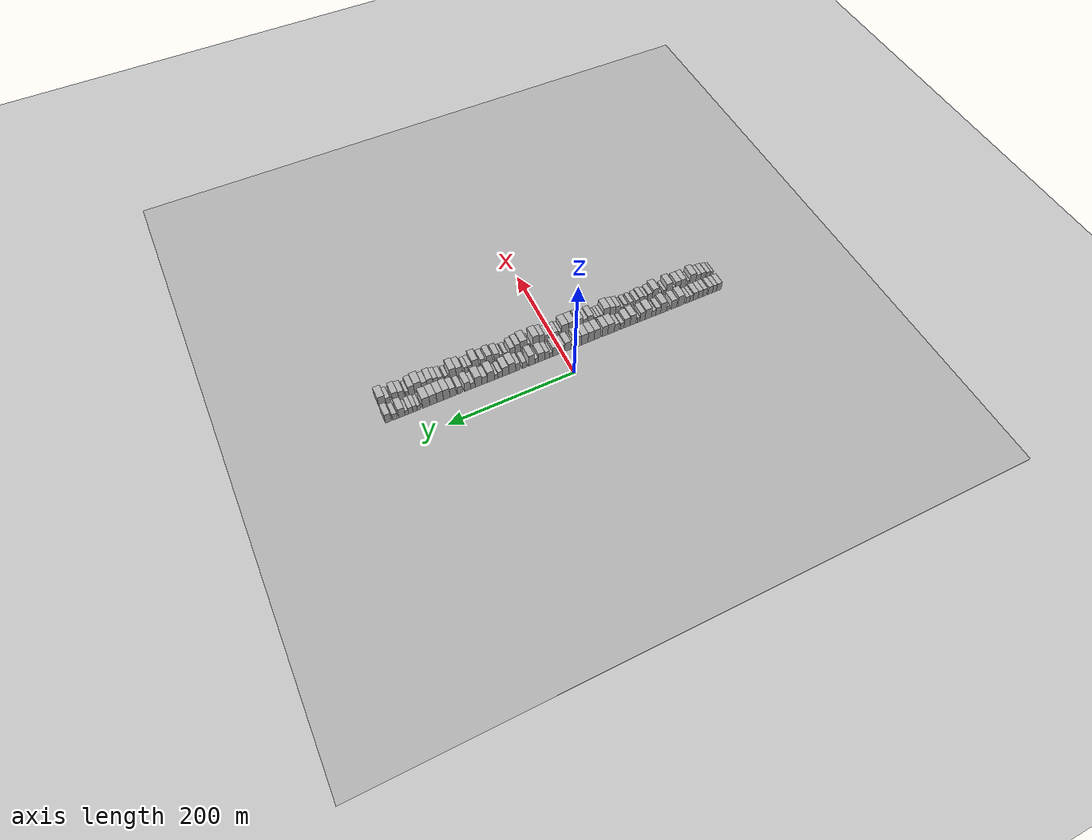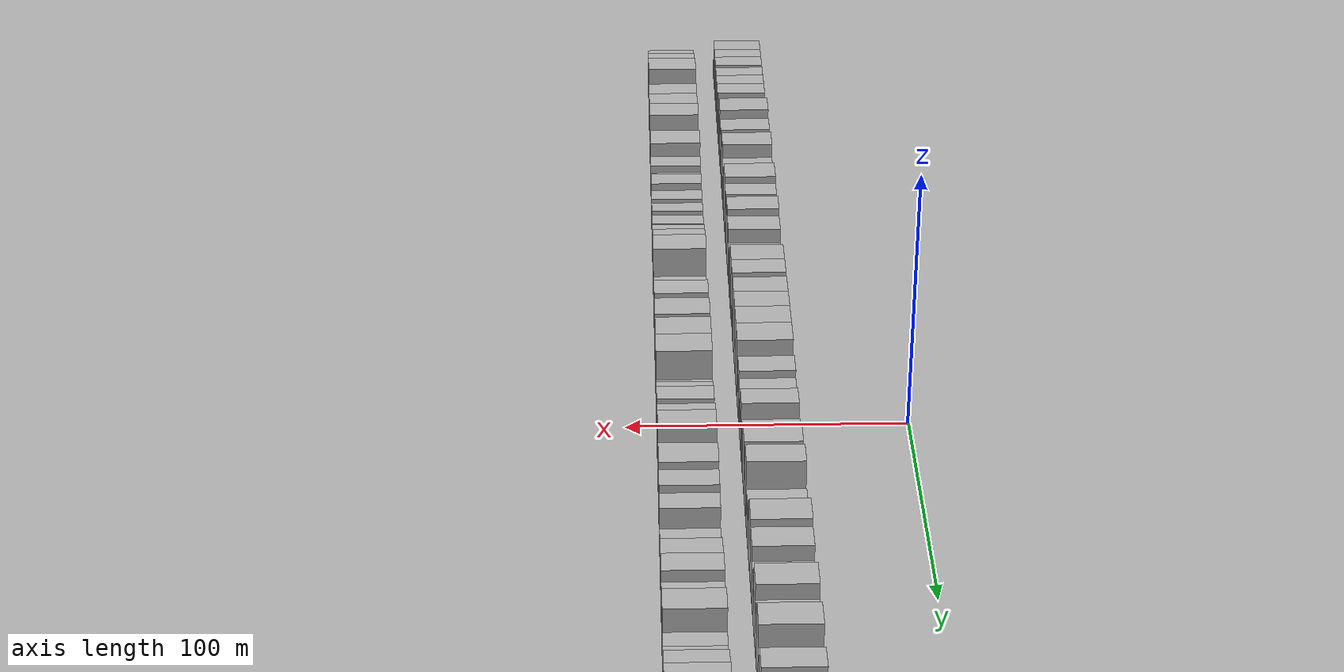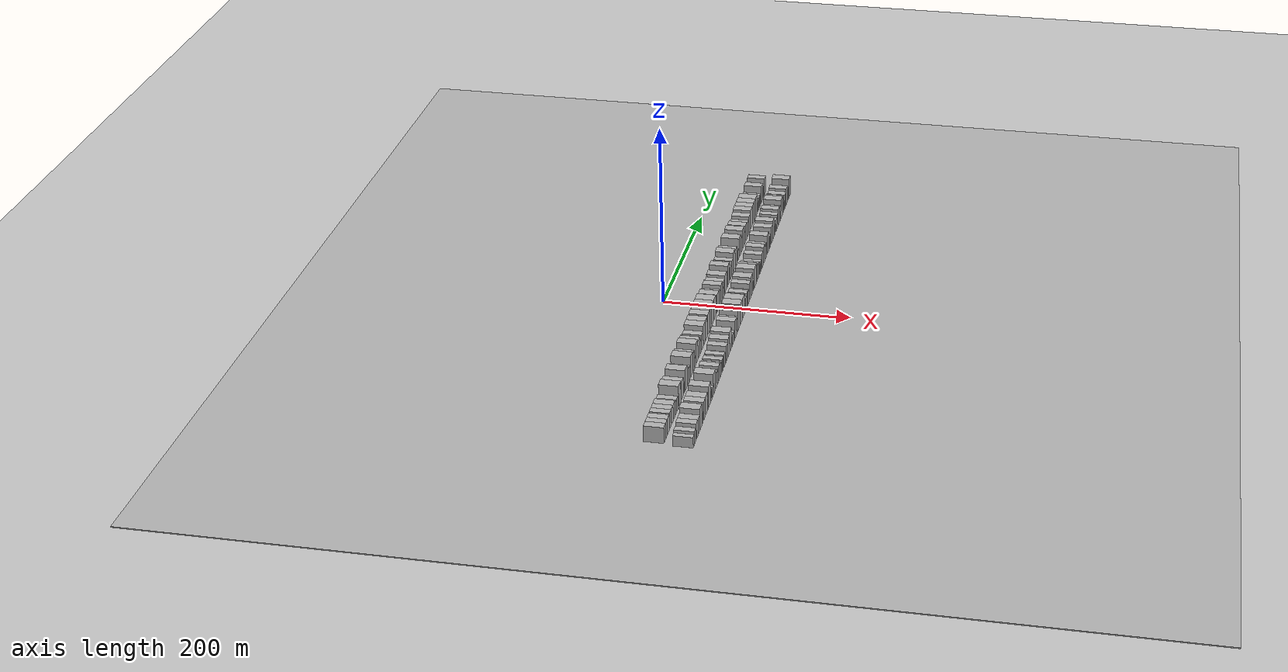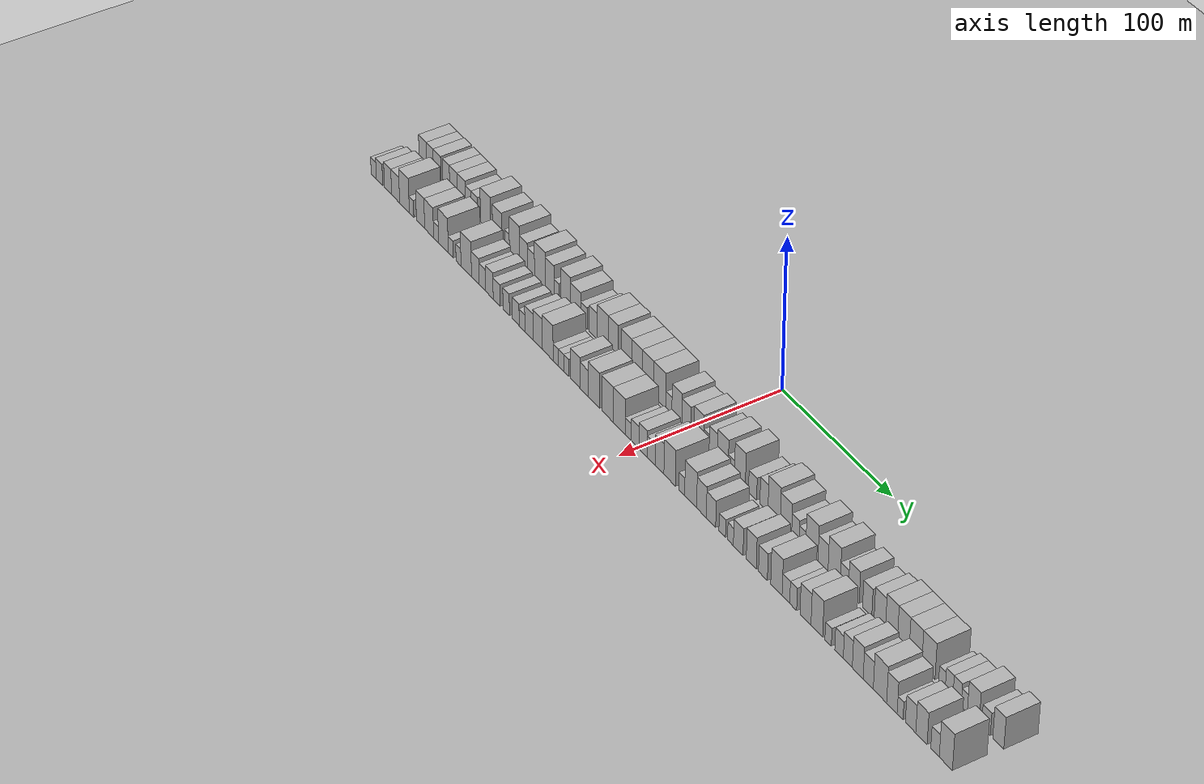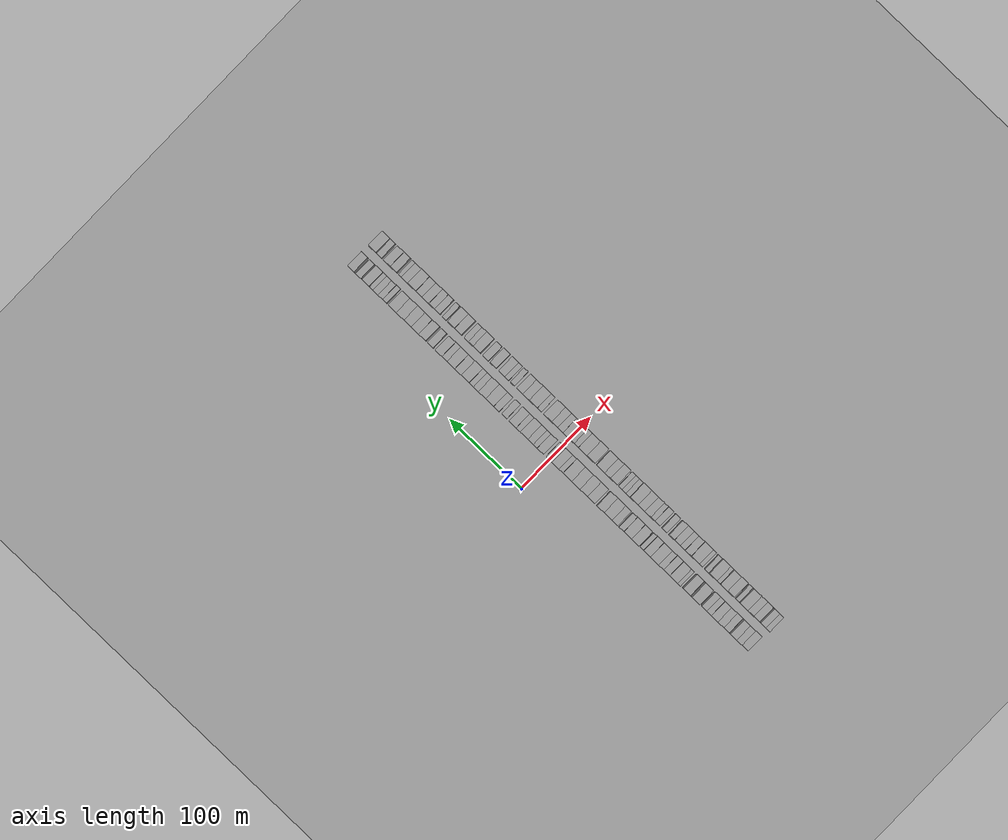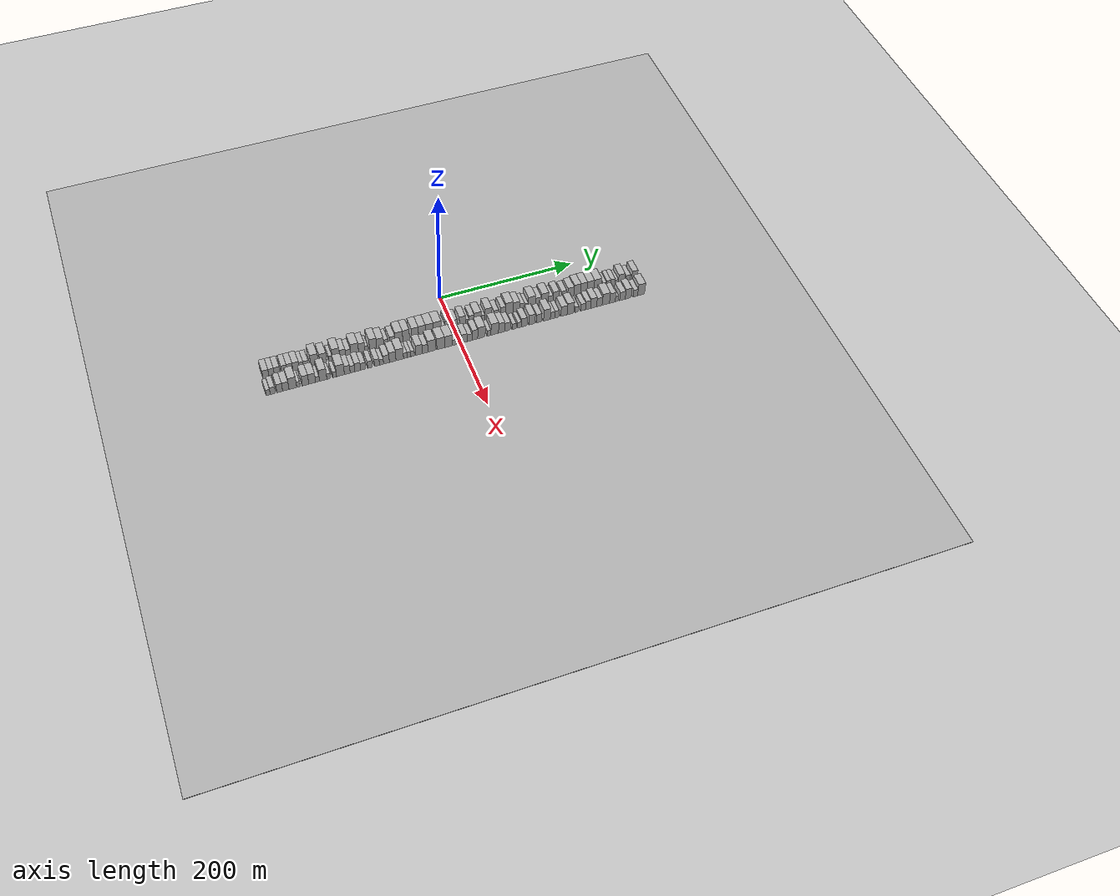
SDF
<?xml version="1.0" encoding="utf-8"?>

<sdf version="1.6">

   <world name="default">

      <gui fullscreen="0">

         <camera name="user_camera">

            <pose>-15 0 4.57585 0 0 0</pose>

            <view_controller>orbit</view_controller>

         </camera>

      </gui>

      <scene>

         <sky>

           <clouds>

             <speed>12</speed>

           </clouds>

         </sky>

         <ambient>0.4 0.4 0.4 1</ambient>

         <background>0.7 0.7 0.7 1</background>

         <shadows>1</shadows>

      </scene>

      <gravity>0 0 -9.8066</gravity>

      <magnetic_field>6e-06 2.3e-05 -4.2e-05</magnetic_field>

      <physics default="0" name="default_physics" type="ode">

         <ode>

            <solver>

               <type>quick</type>

               <iters>10</iters>

               <sor>1.0</sor>

               <use_dynamic_moi_rescaling>0</use_dynamic_moi_rescaling>

            </solver>

            <constraints>

               <cfm>0</cfm>

               <erp>0.2</erp>

               <contact_max_correcting_vel>100</contact_max_correcting_vel>

               <contact_surface_layer>0.001</contact_surface_layer>

            </constraints>

         </ode>

         <max_step_size>0.004</max_step_size>

         <real_time_factor>1</real_time_factor>

         <real_time_update_rate>250</real_time_update_rate>

      </physics>

      <light name="sun" type="directional">

         <cast_shadows>1</cast_shadows>

         <pose>0 0 10 0 0 0</pose>

         <diffuse>0.8 0.8 0.8 1</diffuse>

         <specular>0.2 0.2 0.2 1</specular>

         <attenuation>

            <range>1000</range>

            <constant>0.9</constant>

            <linear>0.01</linear>

            <quadratic>0.001</quadratic>

         </attenuation>

         <direction>-0.5 0.1 -0.9</direction>

      </light>

      <include>

         <name>ground_plane_1</name>

         <uri>model://HANNAS_ground_plane</uri>

         <pose>0 0 0  0 0 0</pose>

      </include>

      <include>

         <name>ground_plane_2</name>

         <uri>model://HANNAS_ground_plane</uri>

         <pose>100 0 0  0 0 0</pose>

      </include>

      <model name="building_1">

         <static>1</static>

         <pose frame="">50.0000 -270.7168 0 0.000000 0.000000 0.000000</pose>

         <link name="link">

            <pose frame="">0 0 9.00 0 0 0</pose>

            <collision name="collision">

               <geometry>

                  <box>

                     <size>20.0000 8.5664 18.0000</size>

                  </box>

               </geometry>

               <max_contacts>10</max_contacts>

               <surface>

                  <contact>

                     <ode/>

                  </contact>

                  <bounce/>

                  <friction>

                     <torsional>

                        <ode/>

                     </torsional>

                     <ode/>

                  </friction>

               </surface>

            </collision>

            <visual name="visual">

               <cast_shadows>0</cast_shadows>

               <geometry>

                  <box>

                     <size>20.0000 8.5664 18.0000</size>

                  </box>

               </geometry>

               <material>

                  <script>

                     <uri>model://HANNAS_wall/materials/scripts</uri>

                     <uri>model://HANNAS_wall/materials/textures</uri>

                     <name>vrc/HANNAS_wall</name>

                  </script>

               </material>

            </visual>

            <self_collide>0</self_collide>

            <enable_wind>0</enable_wind>

            <kinematic>0</kinematic>

         </link>

      </model>

      <model name="building_2">

         <static>1</static>

         <pose frame="">50.0000 -262.7219 0 0.000000 0.000000 0.000000</pose>

         <link name="link">

            <pose frame="">0 0 9.00 0 0 0</pose>

            <collision name="collision">

               <geometry>

                  <box>

                     <size>20.0000 7.4233 18.0000</size>

                  </box>

               </geometry>

               <max_contacts>10</max_contacts>

               <surface>

                  <contact>

                     <ode/>

                  </contact>

                  <bounce/>

                  <friction>

                     <torsional>

                        <ode/>

                     </torsional>

                     <ode/>

                  </friction>

               </surface>

            </collision>

            <visual name="visual">

               <cast_shadows>0</cast_shadows>

               <geometry>

                  <box>

                     <size>20.0000 7.4233 18.0000</size>

                  </box>

               </geometry>

               <material>

                  <script>

                     <uri>model://HANNAS_wall/materials/scripts</uri>

                     <uri>model://HANNAS_wall/materials/textures</uri>

                     <name>vrc/HANNAS_wall</name>

                  </script>

               </material>

            </visual>

            <self_collide>0</self_collide>

            <enable_wind>0</enable_wind>

            <kinematic>0</kinematic>

         </link>

      </model>

      <model name="building_3">

         <static>1</static>

         <pose frame="">50.0000 -254.8419 0 0.000000 0.000000 0.000000</pose>

         <link name="link">

            <pose frame="">0 0 9.00 0 0 0</pose>

            <collision name="collision">

               <geometry>

                  <box>

                     <size>20.0000 8.3367 18.0000</size>

                  </box>

               </geometry>

               <max_contacts>10</max_contacts>

               <surface>

                  <contact>

                     <ode/>

                  </contact>

                  <bounce/>

                  <friction>

                     <torsional>

                        <ode/>

                     </torsional>

                     <ode/>

                  </friction>

               </surface>

            </collision>

            <visual name="visual">

               <cast_shadows>0</cast_shadows>

               <geometry>

                  <box>

                     <size>20.0000 8.3367 18.0000</size>

                  </box>

               </geometry>

               <material>

                  <script>

                     <uri>model://HANNAS_wall/materials/scripts</uri>

                     <uri>model://HANNAS_wall/materials/textures</uri>

                     <name>vrc/HANNAS_wall</name>

                  </script>

               </material>

            </visual>

            <self_collide>0</self_collide>

            <enable_wind>0</enable_wind>

            <kinematic>0</kinematic>

         </link>

      </model>

      <model name="building_4">

         <static>1</static>

         <pose frame="">50.0000 -244.9049 0 0.000000 0.000000 0.000000</pose>

         <link name="link">

            <pose frame="">0 0 9.00 0 0 0</pose>

            <collision name="collision">

               <geometry>

                  <box>

                     <size>20.0000 7.5373 18.0000</size>

                  </box>

               </geometry>

               <max_contacts>10</max_contacts>

               <surface>

                  <contact>

                     <ode/>

                  </contact>

                  <bounce/>

                  <friction>

                     <torsional>

                        <ode/>

                     </torsional>

                     <ode/>

                  </friction>

               </surface>

            </collision>

            <visual name="visual">

               <cast_shadows>0</cast_shadows>

               <geometry>

                  <box>

                     <size>20.0000 7.5373 18.0000</size>

                  </box>

               </geometry>

               <material>

                  <script>

                     <uri>model://HANNAS_wall/materials/scripts</uri>

                     <uri>model://HANNAS_wall/materials/textures</uri>

                     <name>vrc/HANNAS_wall</name>

                  </script>

               </material>

            </visual>

            <self_collide>0</self_collide>

            <enable_wind>0</enable_wind>

            <kinematic>0</kinematic>

         </link>

      </model>

      <model name="building_5">

         <static>1</static>

         <pose frame="">50.0000 -237.0605 0 0.000000 0.000000 0.000000</pose>

         <link name="link">

            <pose frame="">0 0 9.00 0 0 0</pose>

            <collision name="collision">

               <geometry>

                  <box>

                     <size>20.0000 8.1513 18.0000</size>

                  </box>

               </geometry>

               <max_contacts>10</max_contacts>

               <surface>

                  <contact>

                     <ode/>

                  </contact>

                  <bounce/>

                  <friction>

                     <torsional>

                        <ode/>

                     </torsional>

                     <ode/>

                  </friction>

               </surface>

            </collision>

            <visual name="visual">

               <cast_shadows>0</cast_shadows>

               <geometry>

                  <box>

                     <size>20.0000 8.1513 18.0000</size>

                  </box>

               </geometry>

               <material>

                  <script>

                     <uri>model://HANNAS_wall/materials/scripts</uri>

                     <uri>model://HANNAS_wall/materials/textures</uri>

                     <name>vrc/HANNAS_wall</name>

                  </script>

               </material>

            </visual>

            <self_collide>0</self_collide>

            <enable_wind>0</enable_wind>

            <kinematic>0</kinematic>

         </link>

      </model>

      <model name="building_6">

         <static>1</static>

         <pose frame="">50.0000 -228.5198 0 0.000000 0.000000 0.000000</pose>

         <link name="link">

            <pose frame="">0 0 9.00 0 0 0</pose>

            <collision name="collision">

               <geometry>

                  <box>

                     <size>20.0000 8.9301 18.0000</size>

                  </box>

               </geometry>

               <max_contacts>10</max_contacts>

               <surface>

                  <contact>

                     <ode/>

                  </contact>

                  <bounce/>

                  <friction>

                     <torsional>

                        <ode/>

                     </torsional>

                     <ode/>

                  </friction>

               </surface>

            </collision>

            <visual name="visual">

               <cast_shadows>0</cast_shadows>

               <geometry>

                  <box>

                     <size>20.0000 8.9301 18.0000</size>

                  </box>

               </geometry>

               <material>

                  <script>

                     <uri>model://HANNAS_wall/materials/scripts</uri>

                     <uri>model://HANNAS_wall/materials/textures</uri>

                     <name>vrc/HANNAS_wall</name>

                  </script>

               </material>

            </visual>

            <self_collide>0</self_collide>

            <enable_wind>0</enable_wind>

            <kinematic>0</kinematic>

         </link>

      </model>

      <model name="building_7">

         <static>1</static>

         <pose frame="">50.0000 -220.9918 0 0.000000 0.000000 0.000000</pose>

         <link name="link">

            <pose frame="">0 0 7.50 0 0 0</pose>

            <collision name="collision">

               <geometry>

                  <box>

                     <size>20.0000 6.1259 15.0000</size>

                  </box>

               </geometry>

               <max_contacts>10</max_contacts>

               <surface>

                  <contact>

                     <ode/>

                  </contact>

                  <bounce/>

                  <friction>

                     <torsional>

                        <ode/>

                     </torsional>

                     <ode/>

                  </friction>

               </surface>

            </collision>

            <visual name="visual">

               <cast_shadows>0</cast_shadows>

               <geometry>

                  <box>

                     <size>20.0000 6.1259 15.0000</size>

                  </box>

               </geometry>

               <material>

                  <script>

                     <uri>model://HANNAS_wall/materials/scripts</uri>

                     <uri>model://HANNAS_wall/materials/textures</uri>

                     <name>vrc/HANNAS_wall</name>

                  </script>

               </material>

            </visual>

            <self_collide>0</self_collide>

            <enable_wind>0</enable_wind>

            <kinematic>0</kinematic>

         </link>

      </model>

      <model name="building_8">

         <static>1</static>

         <pose frame="">50.0000 -214.3216 0 0.000000 0.000000 0.000000</pose>

         <link name="link">

            <pose frame="">0 0 7.50 0 0 0</pose>

            <collision name="collision">

               <geometry>

                  <box>

                     <size>20.0000 7.2145 15.0000</size>

                  </box>

               </geometry>

               <max_contacts>10</max_contacts>

               <surface>

                  <contact>

                     <ode/>

                  </contact>

                  <bounce/>

                  <friction>

                     <torsional>

                        <ode/>

                     </torsional>

                     <ode/>

                  </friction>

               </surface>

            </collision>

            <visual name="visual">

               <cast_shadows>0</cast_shadows>

               <geometry>

                  <box>

                     <size>20.0000 7.2145 15.0000</size>

                  </box>

               </geometry>

               <material>

                  <script>

                     <uri>model://HANNAS_wall/materials/scripts</uri>

                     <uri>model://HANNAS_wall/materials/textures</uri>

                     <name>vrc/HANNAS_wall</name>

                  </script>

               </material>

            </visual>

            <self_collide>0</self_collide>

            <enable_wind>0</enable_wind>

            <kinematic>0</kinematic>

         </link>

      </model>

      <model name="building_9">

         <static>1</static>

         <pose frame="">50.0000 -202.2630 0 0.000000 0.000000 0.000000</pose>

         <link name="link">

            <pose frame="">0 0 12.00 0 0 0</pose>

            <collision name="collision">

               <geometry>

                  <box>

                     <size>20.0000 10.9027 24.0000</size>

                  </box>

               </geometry>

               <max_contacts>10</max_contacts>

               <surface>

                  <contact>

                     <ode/>

                  </contact>

                  <bounce/>

                  <friction>

                     <torsional>

                        <ode/>

                     </torsional>

                     <ode/>

                  </friction>

               </surface>

            </collision>

            <visual name="visual">

               <cast_shadows>0</cast_shadows>

               <geometry>

                  <box>

                     <size>20.0000 10.9027 24.0000</size>

                  </box>

               </geometry>

               <material>

                  <script>

                     <uri>model://HANNAS_wall/materials/scripts</uri>

                     <uri>model://HANNAS_wall/materials/textures</uri>

                     <name>vrc/HANNAS_wall</name>

                  </script>

               </material>

            </visual>

            <self_collide>0</self_collide>

            <enable_wind>0</enable_wind>

            <kinematic>0</kinematic>

         </link>

      </model>

      <model name="building_10">

         <static>1</static>

         <pose frame="">50.0000 -189.8915 0 0.000000 0.000000 0.000000</pose>

         <link name="link">

            <pose frame="">0 0 10.50 0 0 0</pose>

            <collision name="collision">

               <geometry>

                  <box>

                     <size>20.0000 9.8403 21.0000</size>

                  </box>

               </geometry>

               <max_contacts>10</max_contacts>

               <surface>

                  <contact>

                     <ode/>

                  </contact>

                  <bounce/>

                  <friction>

                     <torsional>

                        <ode/>

                     </torsional>

                     <ode/>

                  </friction>

               </surface>

            </collision>

            <visual name="visual">

               <cast_shadows>0</cast_shadows>

               <geometry>

                  <box>

                     <size>20.0000 9.8403 21.0000</size>

                  </box>

               </geometry>

               <material>

                  <script>

                     <uri>model://HANNAS_wall/materials/scripts</uri>

                     <uri>model://HANNAS_wall/materials/textures</uri>

                     <name>vrc/HANNAS_wall</name>

                  </script>

               </material>

            </visual>

            <self_collide>0</self_collide>

            <enable_wind>0</enable_wind>

            <kinematic>0</kinematic>

         </link>

      </model>

      <model name="building_11">

         <static>1</static>

         <pose frame="">50.0000 -179.4758 0 0.000000 0.000000 0.000000</pose>

         <link name="link">

            <pose frame="">0 0 6.00 0 0 0</pose>

            <collision name="collision">

               <geometry>

                  <box>

                     <size>20.0000 4.9911 12.0000</size>

                  </box>

               </geometry>

               <max_contacts>10</max_contacts>

               <surface>

                  <contact>

                     <ode/>

                  </contact>

                  <bounce/>

                  <friction>

                     <torsional>

                        <ode/>

                     </torsional>

                     <ode/>

                  </friction>

               </surface>

            </collision>

            <visual name="visual">

               <cast_shadows>0</cast_shadows>

               <geometry>

                  <box>

                     <size>20.0000 4.9911 12.0000</size>

                  </box>

               </geometry>

               <material>

                  <script>

                     <uri>model://HANNAS_wall/materials/scripts</uri>

                     <uri>model://HANNAS_wall/materials/textures</uri>

                     <name>vrc/HANNAS_wall</name>

                  </script>

               </material>

            </visual>

            <self_collide>0</self_collide>

            <enable_wind>0</enable_wind>

            <kinematic>0</kinematic>

         </link>

      </model>

      <model name="building_12">

         <static>1</static>

         <pose frame="">50.0000 -171.6714 0 0.000000 0.000000 0.000000</pose>

         <link name="link">

            <pose frame="">0 0 12.00 0 0 0</pose>

            <collision name="collision">

               <geometry>

                  <box>

                     <size>20.0000 10.6177 24.0000</size>

                  </box>

               </geometry>

               <max_contacts>10</max_contacts>

               <surface>

                  <contact>

                     <ode/>

                  </contact>

                  <bounce/>

                  <friction>

                     <torsional>

                        <ode/>

                     </torsional>

                     <ode/>

                  </friction>

               </surface>

            </collision>

            <visual name="visual">

               <cast_shadows>0</cast_shadows>

               <geometry>

                  <box>

                     <size>20.0000 10.6177 24.0000</size>

                  </box>

               </geometry>

               <material>

                  <script>

                     <uri>model://HANNAS_wall/materials/scripts</uri>

                     <uri>model://HANNAS_wall/materials/textures</uri>

                     <name>vrc/HANNAS_wall</name>

                  </script>

               </material>

            </visual>

            <self_collide>0</self_collide>

            <enable_wind>0</enable_wind>

            <kinematic>0</kinematic>

         </link>

      </model>

      <model name="building_13">

         <static>1</static>

         <pose frame="">50.0000 -162.2063 0 0.000000 0.000000 0.000000</pose>

         <link name="link">

            <pose frame="">0 0 9.00 0 0 0</pose>

            <collision name="collision">

               <geometry>

                  <box>

                     <size>20.0000 8.3125 18.0000</size>

                  </box>

               </geometry>

               <max_contacts>10</max_contacts>

               <surface>

                  <contact>

                     <ode/>

                  </contact>

                  <bounce/>

                  <friction>

                     <torsional>

                        <ode/>

                     </torsional>

                     <ode/>

                  </friction>

               </surface>

            </collision>

            <visual name="visual">

               <cast_shadows>0</cast_shadows>

               <geometry>

                  <box>

                     <size>20.0000 8.3125 18.0000</size>

                  </box>

               </geometry>

               <material>

                  <script>

                     <uri>model://HANNAS_wall/materials/scripts</uri>

                     <uri>model://HANNAS_wall/materials/textures</uri>

                     <name>vrc/HANNAS_wall</name>

                  </script>

               </material>

            </visual>

            <self_collide>0</self_collide>

            <enable_wind>0</enable_wind>

            <kinematic>0</kinematic>

         </link>

      </model>

      <model name="building_14">

         <static>1</static>

         <pose frame="">50.0000 -154.3164 0 0.000000 0.000000 0.000000</pose>

         <link name="link">

            <pose frame="">0 0 7.50 0 0 0</pose>

            <collision name="collision">

               <geometry>

                  <box>

                     <size>20.0000 7.4673 15.0000</size>

                  </box>

               </geometry>

               <max_contacts>10</max_contacts>

               <surface>

                  <contact>

                     <ode/>

                  </contact>

                  <bounce/>

                  <friction>

                     <torsional>

                        <ode/>

                     </torsional>

                     <ode/>

                  </friction>

               </surface>

            </collision>

            <visual name="visual">

               <cast_shadows>0</cast_shadows>

               <geometry>

                  <box>

                     <size>20.0000 7.4673 15.0000</size>

                  </box>

               </geometry>

               <material>

                  <script>

                     <uri>model://HANNAS_wall/materials/scripts</uri>

                     <uri>model://HANNAS_wall/materials/textures</uri>

                     <name>vrc/HANNAS_wall</name>

                  </script>

               </material>

            </visual>

            <self_collide>0</self_collide>

            <enable_wind>0</enable_wind>

            <kinematic>0</kinematic>

         </link>

      </model>

      <model name="building_15">

         <static>1</static>

         <pose frame="">50.0000 -144.9487 0 0.000000 0.000000 0.000000</pose>

         <link name="link">

            <pose frame="">0 0 12.00 0 0 0</pose>

            <collision name="collision">

               <geometry>

                  <box>

                     <size>20.0000 11.2681 24.0000</size>

                  </box>

               </geometry>

               <max_contacts>10</max_contacts>

               <surface>

                  <contact>

                     <ode/>

                  </contact>

                  <bounce/>

                  <friction>

                     <torsional>

                        <ode/>

                     </torsional>

                     <ode/>

                  </friction>

               </surface>

            </collision>

            <visual name="visual">

               <cast_shadows>0</cast_shadows>

               <geometry>

                  <box>

                     <size>20.0000 11.2681 24.0000</size>

                  </box>

               </geometry>

               <material>

                  <script>

                     <uri>model://HANNAS_wall/materials/scripts</uri>

                     <uri>model://HANNAS_wall/materials/textures</uri>

                     <name>vrc/HANNAS_wall</name>

                  </script>

               </material>

            </visual>

            <self_collide>0</self_collide>

            <enable_wind>0</enable_wind>

            <kinematic>0</kinematic>

         </link>

      </model>

      <model name="building_16">

         <static>1</static>

         <pose frame="">50.0000 -134.8503 0 0.000000 0.000000 0.000000</pose>

         <link name="link">

            <pose frame="">0 0 10.50 0 0 0</pose>

            <collision name="collision">

               <geometry>

                  <box>

                     <size>20.0000 8.9286 21.0000</size>

                  </box>

               </geometry>

               <max_contacts>10</max_contacts>

               <surface>

                  <contact>

                     <ode/>

                  </contact>

                  <bounce/>

                  <friction>

                     <torsional>

                        <ode/>

                     </torsional>

                     <ode/>

                  </friction>

               </surface>

            </collision>

            <visual name="visual">

               <cast_shadows>0</cast_shadows>

               <geometry>

                  <box>

                     <size>20.0000 8.9286 21.0000</size>

                  </box>

               </geometry>

               <material>

                  <script>

                     <uri>model://HANNAS_wall/materials/scripts</uri>

                     <uri>model://HANNAS_wall/materials/textures</uri>

                     <name>vrc/HANNAS_wall</name>

                  </script>

               </material>

            </visual>

            <self_collide>0</self_collide>

            <enable_wind>0</enable_wind>

            <kinematic>0</kinematic>

         </link>

      </model>

      <model name="building_17">

         <static>1</static>

         <pose frame="">50.0000 -127.9544 0 0.000000 0.000000 0.000000</pose>

         <link name="link">

            <pose frame="">0 0 6.00 0 0 0</pose>

            <collision name="collision">

               <geometry>

                  <box>

                     <size>20.0000 4.8633 12.0000</size>

                  </box>

               </geometry>

               <max_contacts>10</max_contacts>

               <surface>

                  <contact>

                     <ode/>

                  </contact>

                  <bounce/>

                  <friction>

                     <torsional>

                        <ode/>

                     </torsional>

                     <ode/>

                  </friction>

               </surface>

            </collision>

            <visual name="visual">

               <cast_shadows>0</cast_shadows>

               <geometry>

                  <box>

                     <size>20.0000 4.8633 12.0000</size>

                  </box>

               </geometry>

               <material>

                  <script>

                     <uri>model://HANNAS_wall/materials/scripts</uri>

                     <uri>model://HANNAS_wall/materials/textures</uri>

                     <name>vrc/HANNAS_wall</name>

                  </script>

               </material>

            </visual>

            <self_collide>0</self_collide>

            <enable_wind>0</enable_wind>

            <kinematic>0</kinematic>

         </link>

      </model>

      <model name="building_18">

         <static>1</static>

         <pose frame="">50.0000 -118.4666 0 0.000000 0.000000 0.000000</pose>

         <link name="link">

            <pose frame="">0 0 12.00 0 0 0</pose>

            <collision name="collision">

               <geometry>

                  <box>

                     <size>20.0000 10.1121 24.0000</size>

                  </box>

               </geometry>

               <max_contacts>10</max_contacts>

               <surface>

                  <contact>

                     <ode/>

                  </contact>

                  <bounce/>

                  <friction>

                     <torsional>

                        <ode/>

                     </torsional>

                     <ode/>

                  </friction>

               </surface>

            </collision>

            <visual name="visual">

               <cast_shadows>0</cast_shadows>

               <geometry>

                  <box>

                     <size>20.0000 10.1121 24.0000</size>

                  </box>

               </geometry>

               <material>

                  <script>

                     <uri>model://HANNAS_wall/materials/scripts</uri>

                     <uri>model://HANNAS_wall/materials/textures</uri>

                     <name>vrc/HANNAS_wall</name>

                  </script>

               </material>

            </visual>

            <self_collide>0</self_collide>

            <enable_wind>0</enable_wind>

            <kinematic>0</kinematic>

         </link>

      </model>

      <model name="building_19">

         <static>1</static>

         <pose frame="">50.0000 -108.1889 0 0.000000 0.000000 0.000000</pose>

         <link name="link">

            <pose frame="">0 0 10.50 0 0 0</pose>

            <collision name="collision">

               <geometry>

                  <box>

                     <size>20.0000 10.4434 21.0000</size>

                  </box>

               </geometry>

               <max_contacts>10</max_contacts>

               <surface>

                  <contact>

                     <ode/>

                  </contact>

                  <bounce/>

                  <friction>

                     <torsional>

                        <ode/>

                     </torsional>

                     <ode/>

                  </friction>

               </surface>

            </collision>

            <visual name="visual">

               <cast_shadows>0</cast_shadows>

               <geometry>

                  <box>

                     <size>20.0000 10.4434 21.0000</size>

                  </box>

               </geometry>

               <material>

                  <script>

                     <uri>model://HANNAS_wall/materials/scripts</uri>

                     <uri>model://HANNAS_wall/materials/textures</uri>

                     <name>vrc/HANNAS_wall</name>

                  </script>

               </material>

            </visual>

            <self_collide>0</self_collide>

            <enable_wind>0</enable_wind>

            <kinematic>0</kinematic>

         </link>

      </model>

      <model name="building_20">

         <static>1</static>

         <pose frame="">50.0000 -99.7543 0 0.000000 0.000000 0.000000</pose>

         <link name="link">

            <pose frame="">0 0 7.50 0 0 0</pose>

            <collision name="collision">

               <geometry>

                  <box>

                     <size>20.0000 6.4258 15.0000</size>

                  </box>

               </geometry>

               <max_contacts>10</max_contacts>

               <surface>

                  <contact>

                     <ode/>

                  </contact>

                  <bounce/>

                  <friction>

                     <torsional>

                        <ode/>

                     </torsional>

                     <ode/>

                  </friction>

               </surface>

            </collision>

            <visual name="visual">

               <cast_shadows>0</cast_shadows>

               <geometry>

                  <box>

                     <size>20.0000 6.4258 15.0000</size>

                  </box>

               </geometry>

               <material>

                  <script>

                     <uri>model://HANNAS_wall/materials/scripts</uri>

                     <uri>model://HANNAS_wall/materials/textures</uri>

                     <name>vrc/HANNAS_wall</name>

                  </script>

               </material>

            </visual>

            <self_collide>0</self_collide>

            <enable_wind>0</enable_wind>

            <kinematic>0</kinematic>

         </link>

      </model>

      <model name="building_21">

         <static>1</static>

         <pose frame="">50.0000 -90.4187 0 0.000000 0.000000 0.000000</pose>

         <link name="link">

            <pose frame="">0 0 9.00 0 0 0</pose>

            <collision name="collision">

               <geometry>

                  <box>

                     <size>20.0000 8.2455 18.0000</size>

                  </box>

               </geometry>

               <max_contacts>10</max_contacts>

               <surface>

                  <contact>

                     <ode/>

                  </contact>

                  <bounce/>

                  <friction>

                     <torsional>

                        <ode/>

                     </torsional>

                     <ode/>

                  </friction>

               </surface>

            </collision>

            <visual name="visual">

               <cast_shadows>0</cast_shadows>

               <geometry>

                  <box>

                     <size>20.0000 8.2455 18.0000</size>

                  </box>

               </geometry>

               <material>

                  <script>

                     <uri>model://HANNAS_wall/materials/scripts</uri>

                     <uri>model://HANNAS_wall/materials/textures</uri>

                     <name>vrc/HANNAS_wall</name>

                  </script>

               </material>

            </visual>

            <self_collide>0</self_collide>

            <enable_wind>0</enable_wind>

            <kinematic>0</kinematic>

         </link>

      </model>

      <model name="building_22">

         <static>1</static>

         <pose frame="">50.0000 -80.8268 0 0.000000 0.000000 0.000000</pose>

         <link name="link">

            <pose frame="">0 0 12.00 0 0 0</pose>

            <collision name="collision">

               <geometry>

                  <box>

                     <size>20.0000 10.9381 24.0000</size>

                  </box>

               </geometry>

               <max_contacts>10</max_contacts>

               <surface>

                  <contact>

                     <ode/>

                  </contact>

                  <bounce/>

                  <friction>

                     <torsional>

                        <ode/>

                     </torsional>

                     <ode/>

                  </friction>

               </surface>

            </collision>

            <visual name="visual">

               <cast_shadows>0</cast_shadows>

               <geometry>

                  <box>

                     <size>20.0000 10.9381 24.0000</size>

                  </box>

               </geometry>

               <material>

                  <script>

                     <uri>model://HANNAS_wall/materials/scripts</uri>

                     <uri>model://HANNAS_wall/materials/textures</uri>

                     <name>vrc/HANNAS_wall</name>

                  </script>

               </material>

            </visual>

            <self_collide>0</self_collide>

            <enable_wind>0</enable_wind>

            <kinematic>0</kinematic>

         </link>

      </model>

      <model name="building_23">

         <static>1</static>

         <pose frame="">50.0000 -70.4819 0 0.000000 0.000000 0.000000</pose>

         <link name="link">

            <pose frame="">0 0 12.00 0 0 0</pose>

            <collision name="collision">

               <geometry>

                  <box>

                     <size>20.0000 9.7517 24.0000</size>

                  </box>

               </geometry>

               <max_contacts>10</max_contacts>

               <surface>

                  <contact>

                     <ode/>

                  </contact>

                  <bounce/>

                  <friction>

                     <torsional>

                        <ode/>

                     </torsional>

                     <ode/>

                  </friction>

               </surface>

            </collision>

            <visual name="visual">

               <cast_shadows>0</cast_shadows>

               <geometry>

                  <box>

                     <size>20.0000 9.7517 24.0000</size>

                  </box>

               </geometry>

               <material>

                  <script>

                     <uri>model://HANNAS_wall/materials/scripts</uri>

                     <uri>model://HANNAS_wall/materials/textures</uri>

                     <name>vrc/HANNAS_wall</name>

                  </script>

               </material>

            </visual>

            <self_collide>0</self_collide>

            <enable_wind>0</enable_wind>

            <kinematic>0</kinematic>

         </link>

      </model>

      <model name="building_24">

         <static>1</static>

         <pose frame="">50.0000 -57.4572 0 0.000000 0.000000 0.000000</pose>

         <link name="link">

            <pose frame="">0 0 12.00 0 0 0</pose>

            <collision name="collision">

               <geometry>

                  <box>

                     <size>20.0000 10.2979 24.0000</size>

                  </box>

               </geometry>

               <max_contacts>10</max_contacts>

               <surface>

                  <contact>

                     <ode/>

                  </contact>

                  <bounce/>

                  <friction>

                     <torsional>

                        <ode/>

                     </torsional>

                     <ode/>

                  </friction>

               </surface>

            </collision>

            <visual name="visual">

               <cast_shadows>0</cast_shadows>

               <geometry>

                  <box>

                     <size>20.0000 10.2979 24.0000</size>

                  </box>

               </geometry>

               <material>

                  <script>

                     <uri>model://HANNAS_wall/materials/scripts</uri>

                     <uri>model://HANNAS_wall/materials/textures</uri>

                     <name>vrc/HANNAS_wall</name>

                  </script>

               </material>

            </visual>

            <self_collide>0</self_collide>

            <enable_wind>0</enable_wind>

            <kinematic>0</kinematic>

         </link>

      </model>

      <model name="building_25">

         <static>1</static>

         <pose frame="">50.0000 -47.1067 0 0.000000 0.000000 0.000000</pose>

         <link name="link">

            <pose frame="">0 0 12.00 0 0 0</pose>

            <collision name="collision">

               <geometry>

                  <box>

                     <size>20.0000 10.4030 24.0000</size>

                  </box>

               </geometry>

               <max_contacts>10</max_contacts>

               <surface>

                  <contact>

                     <ode/>

                  </contact>

                  <bounce/>

                  <friction>

                     <torsional>

                        <ode/>

                     </torsional>

                     <ode/>

                  </friction>

               </surface>

            </collision>

            <visual name="visual">

               <cast_shadows>0</cast_shadows>

               <geometry>

                  <box>

                     <size>20.0000 10.4030 24.0000</size>

                  </box>

               </geometry>

               <material>

                  <script>

                     <uri>model://HANNAS_wall/materials/scripts</uri>

                     <uri>model://HANNAS_wall/materials/textures</uri>

                     <name>vrc/HANNAS_wall</name>

                  </script>

               </material>

            </visual>

            <self_collide>0</self_collide>

            <enable_wind>0</enable_wind>

            <kinematic>0</kinematic>

         </link>

      </model>

      <model name="building_26">

         <static>1</static>

         <pose frame="">50.0000 -36.2459 0 0.000000 0.000000 0.000000</pose>

         <link name="link">

            <pose frame="">0 0 12.00 0 0 0</pose>

            <collision name="collision">

               <geometry>

                  <box>

                     <size>20.0000 11.3186 24.0000</size>

                  </box>

               </geometry>

               <max_contacts>10</max_contacts>

               <surface>

                  <contact>

                     <ode/>

                  </contact>

                  <bounce/>

                  <friction>

                     <torsional>

                        <ode/>

                     </torsional>

                     <ode/>

                  </friction>

               </surface>

            </collision>

            <visual name="visual">

               <cast_shadows>0</cast_shadows>

               <geometry>

                  <box>

                     <size>20.0000 11.3186 24.0000</size>

                  </box>

               </geometry>

               <material>

                  <script>

                     <uri>model://HANNAS_wall/materials/scripts</uri>

                     <uri>model://HANNAS_wall/materials/textures</uri>

                     <name>vrc/HANNAS_wall</name>

                  </script>

               </material>

            </visual>

            <self_collide>0</self_collide>

            <enable_wind>0</enable_wind>

            <kinematic>0</kinematic>

         </link>

      </model>

      <model name="building_27">

         <static>1</static>

         <pose frame="">50.0000 -24.6920 0 0.000000 0.000000 0.000000</pose>

         <link name="link">

            <pose frame="">0 0 12.00 0 0 0</pose>

            <collision name="collision">

               <geometry>

                  <box>

                     <size>20.0000 11.7893 24.0000</size>

                  </box>

               </geometry>

               <max_contacts>10</max_contacts>

               <surface>

                  <contact>

                     <ode/>

                  </contact>

                  <bounce/>

                  <friction>

                     <torsional>

                        <ode/>

                     </torsional>

                     <ode/>

                  </friction>

               </surface>

            </collision>

            <visual name="visual">

               <cast_shadows>0</cast_shadows>

               <geometry>

                  <box>

                     <size>20.0000 11.7893 24.0000</size>

                  </box>

               </geometry>

               <material>

                  <script>

                     <uri>model://HANNAS_wall/materials/scripts</uri>

                     <uri>model://HANNAS_wall/materials/textures</uri>

                     <name>vrc/HANNAS_wall</name>

                  </script>

               </material>

            </visual>

            <self_collide>0</self_collide>

            <enable_wind>0</enable_wind>

            <kinematic>0</kinematic>

         </link>

      </model>

      <model name="building_28">

         <static>1</static>

         <pose frame="">50.0000 -15.9460 0 0.000000 0.000000 0.000000</pose>

         <link name="link">

            <pose frame="">0 0 6.00 0 0 0</pose>

            <collision name="collision">

               <geometry>

                  <box>

                     <size>20.0000 5.7028 12.0000</size>

                  </box>

               </geometry>

               <max_contacts>10</max_contacts>

               <surface>

                  <contact>

                     <ode/>

                  </contact>

                  <bounce/>

                  <friction>

                     <torsional>

                        <ode/>

                     </torsional>

                     <ode/>

                  </friction>

               </surface>

            </collision>

            <visual name="visual">

               <cast_shadows>0</cast_shadows>

               <geometry>

                  <box>

                     <size>20.0000 5.7028 12.0000</size>

                  </box>

               </geometry>

               <material>

                  <script>

                     <uri>model://HANNAS_wall/materials/scripts</uri>

                     <uri>model://HANNAS_wall/materials/textures</uri>

                     <name>vrc/HANNAS_wall</name>

                  </script>

               </material>

            </visual>

            <self_collide>0</self_collide>

            <enable_wind>0</enable_wind>

            <kinematic>0</kinematic>

         </link>

      </model>

      <model name="building_29">

         <static>1</static>

         <pose frame="">50.0000 -8.2112 0 0.000000 0.000000 0.000000</pose>

         <link name="link">

            <pose frame="">0 0 10.50 0 0 0</pose>

            <collision name="collision">

               <geometry>

                  <box>

                     <size>20.0000 9.7667 21.0000</size>

                  </box>

               </geometry>

               <max_contacts>10</max_contacts>

               <surface>

                  <contact>

                     <ode/>

                  </contact>

                  <bounce/>

                  <friction>

                     <torsional>

                        <ode/>

                     </torsional>

                     <ode/>

                  </friction>

               </surface>

            </collision>

            <visual name="visual">

               <cast_shadows>0</cast_shadows>

               <geometry>

                  <box>

                     <size>20.0000 9.7667 21.0000</size>

                  </box>

               </geometry>

               <material>

                  <script>

                     <uri>model://HANNAS_wall/materials/scripts</uri>

                     <uri>model://HANNAS_wall/materials/textures</uri>

                     <name>vrc/HANNAS_wall</name>

                  </script>

               </material>

            </visual>

            <self_collide>0</self_collide>

            <enable_wind>0</enable_wind>

            <kinematic>0</kinematic>

         </link>

      </model>

      <model name="building_30">

         <static>1</static>

         <pose frame="">50.0000 0.7794 0 0.000000 0.000000 0.000000</pose>

         <link name="link">

            <pose frame="">0 0 9.00 0 0 0</pose>

            <collision name="collision">

               <geometry>

                  <box>

                     <size>20.0000 8.2147 18.0000</size>

                  </box>

               </geometry>

               <max_contacts>10</max_contacts>

               <surface>

                  <contact>

                     <ode/>

                  </contact>

                  <bounce/>

                  <friction>

                     <torsional>

                        <ode/>

                     </torsional>

                     <ode/>

                  </friction>

               </surface>

            </collision>

            <visual name="visual">

               <cast_shadows>0</cast_shadows>

               <geometry>

                  <box>

                     <size>20.0000 8.2147 18.0000</size>

                  </box>

               </geometry>

               <material>

                  <script>

                     <uri>model://HANNAS_wall/materials/scripts</uri>

                     <uri>model://HANNAS_wall/materials/textures</uri>

                     <name>vrc/HANNAS_wall</name>

                  </script>

               </material>

            </visual>

            <self_collide>0</self_collide>

            <enable_wind>0</enable_wind>

            <kinematic>0</kinematic>

         </link>

      </model>

      <model name="building_31">

         <static>1</static>

         <pose frame="">50.0000 12.4411 0 0.000000 0.000000 0.000000</pose>

         <link name="link">

            <pose frame="">0 0 10.50 0 0 0</pose>

            <collision name="collision">

               <geometry>

                  <box>

                     <size>20.0000 9.1086 21.0000</size>

                  </box>

               </geometry>

               <max_contacts>10</max_contacts>

               <surface>

                  <contact>

                     <ode/>

                  </contact>

                  <bounce/>

                  <friction>

                     <torsional>

                        <ode/>

                     </torsional>

                     <ode/>

                  </friction>

               </surface>

            </collision>

            <visual name="visual">

               <cast_shadows>0</cast_shadows>

               <geometry>

                  <box>

                     <size>20.0000 9.1086 21.0000</size>

                  </box>

               </geometry>

               <material>

                  <script>

                     <uri>model://HANNAS_wall/materials/scripts</uri>

                     <uri>model://HANNAS_wall/materials/textures</uri>

                     <name>vrc/HANNAS_wall</name>

                  </script>

               </material>

            </visual>

            <self_collide>0</self_collide>

            <enable_wind>0</enable_wind>

            <kinematic>0</kinematic>

         </link>

      </model>

      <model name="building_32">

         <static>1</static>

         <pose frame="">50.0000 19.7043 0 0.000000 0.000000 0.000000</pose>

         <link name="link">

            <pose frame="">0 0 6.00 0 0 0</pose>

            <collision name="collision">

               <geometry>

                  <box>

                     <size>20.0000 5.4179 12.0000</size>

                  </box>

               </geometry>

               <max_contacts>10</max_contacts>

               <surface>

                  <contact>

                     <ode/>

                  </contact>

                  <bounce/>

                  <friction>

                     <torsional>

                        <ode/>

                     </torsional>

                     <ode/>

                  </friction>

               </surface>

            </collision>

            <visual name="visual">

               <cast_shadows>0</cast_shadows>

               <geometry>

                  <box>

                     <size>20.0000 5.4179 12.0000</size>

                  </box>

               </geometry>

               <material>

                  <script>

                     <uri>model://HANNAS_wall/materials/scripts</uri>

                     <uri>model://HANNAS_wall/materials/textures</uri>

                     <name>vrc/HANNAS_wall</name>

                  </script>

               </material>

            </visual>

            <self_collide>0</self_collide>

            <enable_wind>0</enable_wind>

            <kinematic>0</kinematic>

         </link>

      </model>

      <model name="building_33">

         <static>1</static>

         <pose frame="">50.0000 26.1778 0 0.000000 0.000000 0.000000</pose>

         <link name="link">

            <pose frame="">0 0 9.00 0 0 0</pose>

            <collision name="collision">

               <geometry>

                  <box>

                     <size>20.0000 7.5290 18.0000</size>

                  </box>

               </geometry>

               <max_contacts>10</max_contacts>

               <surface>

                  <contact>

                     <ode/>

                  </contact>

                  <bounce/>

                  <friction>

                     <torsional>

                        <ode/>

                     </torsional>

                     <ode/>

                  </friction>

               </surface>

            </collision>

            <visual name="visual">

               <cast_shadows>0</cast_shadows>

               <geometry>

                  <box>

                     <size>20.0000 7.5290 18.0000</size>

                  </box>

               </geometry>

               <material>

                  <script>

                     <uri>model://HANNAS_wall/materials/scripts</uri>

                     <uri>model://HANNAS_wall/materials/textures</uri>

                     <name>vrc/HANNAS_wall</name>

                  </script>

               </material>

            </visual>

            <self_collide>0</self_collide>

            <enable_wind>0</enable_wind>

            <kinematic>0</kinematic>

         </link>

      </model>

      <model name="building_34">

         <static>1</static>

         <pose frame="">50.0000 35.1295 0 0.000000 0.000000 0.000000</pose>

         <link name="link">

            <pose frame="">0 0 10.50 0 0 0</pose>

            <collision name="collision">

               <geometry>

                  <box>

                     <size>20.0000 10.3746 21.0000</size>

                  </box>

               </geometry>

               <max_contacts>10</max_contacts>

               <surface>

                  <contact>

                     <ode/>

                  </contact>

                  <bounce/>

                  <friction>

                     <torsional>

                        <ode/>

                     </torsional>

                     <ode/>

                  </friction>

               </surface>

            </collision>

            <visual name="visual">

               <cast_shadows>0</cast_shadows>

               <geometry>

                  <box>

                     <size>20.0000 10.3746 21.0000</size>

                  </box>

               </geometry>

               <material>

                  <script>

                     <uri>model://HANNAS_wall/materials/scripts</uri>

                     <uri>model://HANNAS_wall/materials/textures</uri>

                     <name>vrc/HANNAS_wall</name>

                  </script>

               </material>

            </visual>

            <self_collide>0</self_collide>

            <enable_wind>0</enable_wind>

            <kinematic>0</kinematic>

         </link>

      </model>

      <model name="building_35">

         <static>1</static>

         <pose frame="">50.0000 43.2426 0 0.000000 0.000000 0.000000</pose>

         <link name="link">

            <pose frame="">0 0 6.00 0 0 0</pose>

            <collision name="collision">

               <geometry>

                  <box>

                     <size>20.0000 5.8516 12.0000</size>

                  </box>

               </geometry>

               <max_contacts>10</max_contacts>

               <surface>

                  <contact>

                     <ode/>

                  </contact>

                  <bounce/>

                  <friction>

                     <torsional>

                        <ode/>

                     </torsional>

                     <ode/>

                  </friction>

               </surface>

            </collision>

            <visual name="visual">

               <cast_shadows>0</cast_shadows>

               <geometry>

                  <box>

                     <size>20.0000 5.8516 12.0000</size>

                  </box>

               </geometry>

               <material>

                  <script>

                     <uri>model://HANNAS_wall/materials/scripts</uri>

                     <uri>model://HANNAS_wall/materials/textures</uri>

                     <name>vrc/HANNAS_wall</name>

                  </script>

               </material>

            </visual>

            <self_collide>0</self_collide>

            <enable_wind>0</enable_wind>

            <kinematic>0</kinematic>

         </link>

      </model>

      <model name="building_36">

         <static>1</static>

         <pose frame="">50.0000 51.1862 0 0.000000 0.000000 0.000000</pose>

         <link name="link">

            <pose frame="">0 0 12.00 0 0 0</pose>

            <collision name="collision">

               <geometry>

                  <box>

                     <size>20.0000 10.0354 24.0000</size>

                  </box>

               </geometry>

               <max_contacts>10</max_contacts>

               <surface>

                  <contact>

                     <ode/>

                  </contact>

                  <bounce/>

                  <friction>

                     <torsional>

                        <ode/>

                     </torsional>

                     <ode/>

                  </friction>

               </surface>

            </collision>

            <visual name="visual">

               <cast_shadows>0</cast_shadows>

               <geometry>

                  <box>

                     <size>20.0000 10.0354 24.0000</size>

                  </box>

               </geometry>

               <material>

                  <script>

                     <uri>model://HANNAS_wall/materials/scripts</uri>

                     <uri>model://HANNAS_wall/materials/textures</uri>

                     <name>vrc/HANNAS_wall</name>

                  </script>

               </material>

            </visual>

            <self_collide>0</self_collide>

            <enable_wind>0</enable_wind>

            <kinematic>0</kinematic>

         </link>

      </model>

      <model name="building_37">

         <static>1</static>

         <pose frame="">50.0000 62.9248 0 0.000000 0.000000 0.000000</pose>

         <link name="link">

            <pose frame="">0 0 7.50 0 0 0</pose>

            <collision name="collision">

               <geometry>

                  <box>

                     <size>20.0000 7.4419 15.0000</size>

                  </box>

               </geometry>

               <max_contacts>10</max_contacts>

               <surface>

                  <contact>

                     <ode/>

                  </contact>

                  <bounce/>

                  <friction>

                     <torsional>

                        <ode/>

                     </torsional>

                     <ode/>

                  </friction>

               </surface>

            </collision>

            <visual name="visual">

               <cast_shadows>0</cast_shadows>

               <geometry>

                  <box>

                     <size>20.0000 7.4419 15.0000</size>

                  </box>

               </geometry>

               <material>

                  <script>

                     <uri>model://HANNAS_wall/materials/scripts</uri>

                     <uri>model://HANNAS_wall/materials/textures</uri>

                     <name>vrc/HANNAS_wall</name>

                  </script>

               </material>

            </visual>

            <self_collide>0</self_collide>

            <enable_wind>0</enable_wind>

            <kinematic>0</kinematic>

         </link>

      </model>

      <model name="building_38">

         <static>1</static>

         <pose frame="">50.0000 73.3341 0 0.000000 0.000000 0.000000</pose>

         <link name="link">

            <pose frame="">0 0 9.00 0 0 0</pose>

            <collision name="collision">

               <geometry>

                  <box>

                     <size>20.0000 7.3767 18.0000</size>

                  </box>

               </geometry>

               <max_contacts>10</max_contacts>

               <surface>

                  <contact>

                     <ode/>

                  </contact>

                  <bounce/>

                  <friction>

                     <torsional>

                        <ode/>

                     </torsional>

                     <ode/>

                  </friction>

               </surface>

            </collision>

            <visual name="visual">

               <cast_shadows>0</cast_shadows>

               <geometry>

                  <box>

                     <size>20.0000 7.3767 18.0000</size>

                  </box>

               </geometry>

               <material>

                  <script>

                     <uri>model://HANNAS_wall/materials/scripts</uri>

                     <uri>model://HANNAS_wall/materials/textures</uri>

                     <name>vrc/HANNAS_wall</name>

                  </script>

               </material>

            </visual>

            <self_collide>0</self_collide>

            <enable_wind>0</enable_wind>

            <kinematic>0</kinematic>

         </link>

      </model>

      <model name="building_39">

         <static>1</static>

         <pose frame="">50.0000 82.6003 0 0.000000 0.000000 0.000000</pose>

         <link name="link">

            <pose frame="">0 0 12.00 0 0 0</pose>

            <collision name="collision">

               <geometry>

                  <box>

                     <size>20.0000 11.1556 24.0000</size>

                  </box>

               </geometry>

               <max_contacts>10</max_contacts>

               <surface>

                  <contact>

                     <ode/>

                  </contact>

                  <bounce/>

                  <friction>

                     <torsional>

                        <ode/>

                     </torsional>

                     <ode/>

                  </friction>

               </surface>

            </collision>

            <visual name="visual">

               <cast_shadows>0</cast_shadows>

               <geometry>

                  <box>

                     <size>20.0000 11.1556 24.0000</size>

                  </box>

               </geometry>

               <material>

                  <script>

                     <uri>model://HANNAS_wall/materials/scripts</uri>

                     <uri>model://HANNAS_wall/materials/textures</uri>

                     <name>vrc/HANNAS_wall</name>

                  </script>

               </material>

            </visual>

            <self_collide>0</self_collide>

            <enable_wind>0</enable_wind>

            <kinematic>0</kinematic>

         </link>

      </model>

      <model name="building_40">

         <static>1</static>

         <pose frame="">50.0000 93.3117 0 0.000000 0.000000 0.000000</pose>

         <link name="link">

            <pose frame="">0 0 10.50 0 0 0</pose>

            <collision name="collision">

               <geometry>

                  <box>

                     <size>20.0000 10.2672 21.0000</size>

                  </box>

               </geometry>

               <max_contacts>10</max_contacts>

               <surface>

                  <contact>

                     <ode/>

                  </contact>

                  <bounce/>

                  <friction>

                     <torsional>

                        <ode/>

                     </torsional>

                     <ode/>

                  </friction>

               </surface>

            </collision>

            <visual name="visual">

               <cast_shadows>0</cast_shadows>

               <geometry>

                  <box>

                     <size>20.0000 10.2672 21.0000</size>

                  </box>

               </geometry>

               <material>

                  <script>

                     <uri>model://HANNAS_wall/materials/scripts</uri>

                     <uri>model://HANNAS_wall/materials/textures</uri>

                     <name>vrc/HANNAS_wall</name>

                  </script>

               </material>

            </visual>

            <self_collide>0</self_collide>

            <enable_wind>0</enable_wind>

            <kinematic>0</kinematic>

         </link>

      </model>

      <model name="building_41">

         <static>1</static>

         <pose frame="">50.0000 101.8601 0 0.000000 0.000000 0.000000</pose>

         <link name="link">

            <pose frame="">0 0 7.50 0 0 0</pose>

            <collision name="collision">

               <geometry>

                  <box>

                     <size>20.0000 6.8297 15.0000</size>

                  </box>

               </geometry>

               <max_contacts>10</max_contacts>

               <surface>

                  <contact>

                     <ode/>

                  </contact>

                  <bounce/>

                  <friction>

                     <torsional>

                        <ode/>

                     </torsional>

                     <ode/>

                  </friction>

               </surface>

            </collision>

            <visual name="visual">

               <cast_shadows>0</cast_shadows>

               <geometry>

                  <box>

                     <size>20.0000 6.8297 15.0000</size>

                  </box>

               </geometry>

               <material>

                  <script>

                     <uri>model://HANNAS_wall/materials/scripts</uri>

                     <uri>model://HANNAS_wall/materials/textures</uri>

                     <name>vrc/HANNAS_wall</name>

                  </script>

               </material>

            </visual>

            <self_collide>0</self_collide>

            <enable_wind>0</enable_wind>

            <kinematic>0</kinematic>

         </link>

      </model>

      <model name="building_42">

         <static>1</static>

         <pose frame="">50.0000 108.1862 0 0.000000 0.000000 0.000000</pose>

         <link name="link">

            <pose frame="">0 0 6.00 0 0 0</pose>

            <collision name="collision">

               <geometry>

                  <box>

                     <size>20.0000 5.8223 12.0000</size>

                  </box>

               </geometry>

               <max_contacts>10</max_contacts>

               <surface>

                  <contact>

                     <ode/>

                  </contact>

                  <bounce/>

                  <friction>

                     <torsional>

                        <ode/>

                     </torsional>

                     <ode/>

                  </friction>

               </surface>

            </collision>

            <visual name="visual">

               <cast_shadows>0</cast_shadows>

               <geometry>

                  <box>

                     <size>20.0000 5.8223 12.0000</size>

                  </box>

               </geometry>

               <material>

                  <script>

                     <uri>model://HANNAS_wall/materials/scripts</uri>

                     <uri>model://HANNAS_wall/materials/textures</uri>

                     <name>vrc/HANNAS_wall</name>

                  </script>

               </material>

            </visual>

            <self_collide>0</self_collide>

            <enable_wind>0</enable_wind>

            <kinematic>0</kinematic>

         </link>

      </model>

      <model name="building_43">

         <static>1</static>

         <pose frame="">50.0000 116.5472 0 0.000000 0.000000 0.000000</pose>

         <link name="link">

            <pose frame="">0 0 12.00 0 0 0</pose>

            <collision name="collision">

               <geometry>

                  <box>

                     <size>20.0000 10.8998 24.0000</size>

                  </box>

               </geometry>

               <max_contacts>10</max_contacts>

               <surface>

                  <contact>

                     <ode/>

                  </contact>

                  <bounce/>

                  <friction>

                     <torsional>

                        <ode/>

                     </torsional>

                     <ode/>

                  </friction>

               </surface>

            </collision>

            <visual name="visual">

               <cast_shadows>0</cast_shadows>

               <geometry>

                  <box>

                     <size>20.0000 10.8998 24.0000</size>

                  </box>

               </geometry>

               <material>

                  <script>

                     <uri>model://HANNAS_wall/materials/scripts</uri>

                     <uri>model://HANNAS_wall/materials/textures</uri>

                     <name>vrc/HANNAS_wall</name>

                  </script>

               </material>

            </visual>

            <self_collide>0</self_collide>

            <enable_wind>0</enable_wind>

            <kinematic>0</kinematic>

         </link>

      </model>

      <model name="building_44">

         <static>1</static>

         <pose frame="">50.0000 126.4586 0 0.000000 0.000000 0.000000</pose>

         <link name="link">

            <pose frame="">0 0 9.00 0 0 0</pose>

            <collision name="collision">

               <geometry>

                  <box>

                     <size>20.0000 8.9230 18.0000</size>

                  </box>

               </geometry>

               <max_contacts>10</max_contacts>

               <surface>

                  <contact>

                     <ode/>

                  </contact>

                  <bounce/>

                  <friction>

                     <torsional>

                        <ode/>

                     </torsional>

                     <ode/>

                  </friction>

               </surface>

            </collision>

            <visual name="visual">

               <cast_shadows>0</cast_shadows>

               <geometry>

                  <box>

                     <size>20.0000 8.9230 18.0000</size>

                  </box>

               </geometry>

               <material>

                  <script>

                     <uri>model://HANNAS_wall/materials/scripts</uri>

                     <uri>model://HANNAS_wall/materials/textures</uri>

                     <name>vrc/HANNAS_wall</name>

                  </script>

               </material>

            </visual>

            <self_collide>0</self_collide>

            <enable_wind>0</enable_wind>

            <kinematic>0</kinematic>

         </link>

      </model>

      <model name="building_45">

         <static>1</static>

         <pose frame="">50.0000 136.2764 0 0.000000 0.000000 0.000000</pose>

         <link name="link">

            <pose frame="">0 0 12.00 0 0 0</pose>

            <collision name="collision">

               <geometry>

                  <box>

                     <size>20.0000 10.7124 24.0000</size>

                  </box>

               </geometry>

               <max_contacts>10</max_contacts>

               <surface>

                  <contact>

                     <ode/>

                  </contact>

                  <bounce/>

                  <friction>

                     <torsional>

                        <ode/>

                     </torsional>

                     <ode/>

                  </friction>

               </surface>

            </collision>

            <visual name="visual">

               <cast_shadows>0</cast_shadows>

               <geometry>

                  <box>

                     <size>20.0000 10.7124 24.0000</size>

                  </box>

               </geometry>

               <material>

                  <script>

                     <uri>model://HANNAS_wall/materials/scripts</uri>

                     <uri>model://HANNAS_wall/materials/textures</uri>

                     <name>vrc/HANNAS_wall</name>

                  </script>

               </material>

            </visual>

            <self_collide>0</self_collide>

            <enable_wind>0</enable_wind>

            <kinematic>0</kinematic>

         </link>

      </model>

      <model name="building_46">

         <static>1</static>

         <pose frame="">50.0000 145.2257 0 0.000000 0.000000 0.000000</pose>

         <link name="link">

            <pose frame="">0 0 7.50 0 0 0</pose>

            <collision name="collision">

               <geometry>

                  <box>

                     <size>20.0000 7.1862 15.0000</size>

                  </box>

               </geometry>

               <max_contacts>10</max_contacts>

               <surface>

                  <contact>

                     <ode/>

                  </contact>

                  <bounce/>

                  <friction>

                     <torsional>

                        <ode/>

                     </torsional>

                     <ode/>

                  </friction>

               </surface>

            </collision>

            <visual name="visual">

               <cast_shadows>0</cast_shadows>

               <geometry>

                  <box>

                     <size>20.0000 7.1862 15.0000</size>

                  </box>

               </geometry>

               <material>

                  <script>

                     <uri>model://HANNAS_wall/materials/scripts</uri>

                     <uri>model://HANNAS_wall/materials/textures</uri>

                     <name>vrc/HANNAS_wall</name>

                  </script>

               </material>

            </visual>

            <self_collide>0</self_collide>

            <enable_wind>0</enable_wind>

            <kinematic>0</kinematic>

         </link>

      </model>

      <model name="building_47">

         <static>1</static>

         <pose frame="">50.0000 153.5088 0 0.000000 0.000000 0.000000</pose>

         <link name="link">

            <pose frame="">0 0 10.50 0 0 0</pose>

            <collision name="collision">

               <geometry>

                  <box>

                     <size>20.0000 9.3801 21.0000</size>

                  </box>

               </geometry>

               <max_contacts>10</max_contacts>

               <surface>

                  <contact>

                     <ode/>

                  </contact>

                  <bounce/>

                  <friction>

                     <torsional>

                        <ode/>

                     </torsional>

                     <ode/>

                  </friction>

               </surface>

            </collision>

            <visual name="visual">

               <cast_shadows>0</cast_shadows>

               <geometry>

                  <box>

                     <size>20.0000 9.3801 21.0000</size>

                  </box>

               </geometry>

               <material>

                  <script>

                     <uri>model://HANNAS_wall/materials/scripts</uri>

                     <uri>model://HANNAS_wall/materials/textures</uri>

                     <name>vrc/HANNAS_wall</name>

                  </script>

               </material>

            </visual>

            <self_collide>0</self_collide>

            <enable_wind>0</enable_wind>

            <kinematic>0</kinematic>

         </link>

      </model>

      <model name="building_48">

         <static>1</static>

         <pose frame="">50.0000 165.1900 0 0.000000 0.000000 0.000000</pose>

         <link name="link">

            <pose frame="">0 0 9.00 0 0 0</pose>

            <collision name="collision">

               <geometry>

                  <box>

                     <size>20.0000 7.9823 18.0000</size>

                  </box>

               </geometry>

               <max_contacts>10</max_contacts>

               <surface>

                  <contact>

                     <ode/>

                  </contact>

                  <bounce/>

                  <friction>

                     <torsional>

                        <ode/>

                     </torsional>

                     <ode/>

                  </friction>

               </surface>

            </collision>

            <visual name="visual">

               <cast_shadows>0</cast_shadows>

               <geometry>

                  <box>

                     <size>20.0000 7.9823 18.0000</size>

                  </box>

               </geometry>

               <material>

                  <script>

                     <uri>model://HANNAS_wall/materials/scripts</uri>

                     <uri>model://HANNAS_wall/materials/textures</uri>

                     <name>vrc/HANNAS_wall</name>

                  </script>

               </material>

            </visual>

            <self_collide>0</self_collide>

            <enable_wind>0</enable_wind>

            <kinematic>0</kinematic>

         </link>

      </model>

      <model name="building_49">

         <static>1</static>

         <pose frame="">50.0000 176.0217 0 0.000000 0.000000 0.000000</pose>

         <link name="link">

            <pose frame="">0 0 10.50 0 0 0</pose>

            <collision name="collision">

               <geometry>

                  <box>

                     <size>20.0000 9.6810 21.0000</size>

                  </box>

               </geometry>

               <max_contacts>10</max_contacts>

               <surface>

                  <contact>

                     <ode/>

                  </contact>

                  <bounce/>

                  <friction>

                     <torsional>

                        <ode/>

                     </torsional>

                     <ode/>

                  </friction>

               </surface>

            </collision>

            <visual name="visual">

               <cast_shadows>0</cast_shadows>

               <geometry>

                  <box>

                     <size>20.0000 9.6810 21.0000</size>

                  </box>

               </geometry>

               <material>

                  <script>

                     <uri>model://HANNAS_wall/materials/scripts</uri>

                     <uri>model://HANNAS_wall/materials/textures</uri>

                     <name>vrc/HANNAS_wall</name>

                  </script>

               </material>

            </visual>

            <self_collide>0</self_collide>

            <enable_wind>0</enable_wind>

            <kinematic>0</kinematic>

         </link>

      </model>

      <model name="building_50">

         <static>1</static>

         <pose frame="">50.0000 185.9524 0 0.000000 0.000000 0.000000</pose>

         <link name="link">

            <pose frame="">0 0 12.00 0 0 0</pose>

            <collision name="collision">

               <geometry>

                  <box>

                     <size>20.0000 10.1804 24.0000</size>

                  </box>

               </geometry>

               <max_contacts>10</max_contacts>

               <surface>

                  <contact>

                     <ode/>

                  </contact>

                  <bounce/>

                  <friction>

                     <torsional>

                        <ode/>

                     </torsional>

                     <ode/>

                  </friction>

               </surface>

            </collision>

            <visual name="visual">

               <cast_shadows>0</cast_shadows>

               <geometry>

                  <box>

                     <size>20.0000 10.1804 24.0000</size>

                  </box>

               </geometry>

               <material>

                  <script>

                     <uri>model://HANNAS_wall/materials/scripts</uri>

                     <uri>model://HANNAS_wall/materials/textures</uri>

                     <name>vrc/HANNAS_wall</name>

                  </script>

               </material>

            </visual>

            <self_collide>0</self_collide>

            <enable_wind>0</enable_wind>

            <kinematic>0</kinematic>

         </link>

      </model>

      <model name="building_51">

         <static>1</static>

         <pose frame="">50.0000 196.0034 0 0.000000 0.000000 0.000000</pose>

         <link name="link">

            <pose frame="">0 0 12.00 0 0 0</pose>

            <collision name="collision">

               <geometry>

                  <box>

                     <size>20.0000 9.9217 24.0000</size>

                  </box>

               </geometry>

               <max_contacts>10</max_contacts>

               <surface>

                  <contact>

                     <ode/>

                  </contact>

                  <bounce/>

                  <friction>

                     <torsional>

                        <ode/>

                     </torsional>

                     <ode/>

                  </friction>

               </surface>

            </collision>

            <visual name="visual">

               <cast_shadows>0</cast_shadows>

               <geometry>

                  <box>

                     <size>20.0000 9.9217 24.0000</size>

                  </box>

               </geometry>

               <material>

                  <script>

                     <uri>model://HANNAS_wall/materials/scripts</uri>

                     <uri>model://HANNAS_wall/materials/textures</uri>

                     <name>vrc/HANNAS_wall</name>

                  </script>

               </material>

            </visual>

            <self_collide>0</self_collide>

            <enable_wind>0</enable_wind>

            <kinematic>0</kinematic>

         </link>

      </model>

      <model name="building_52">

         <static>1</static>

         <pose frame="">50.0000 206.3297 0 0.000000 0.000000 0.000000</pose>

         <link name="link">

            <pose frame="">0 0 12.00 0 0 0</pose>

            <collision name="collision">

               <geometry>

                  <box>

                     <size>20.0000 10.7308 24.0000</size>

                  </box>

               </geometry>

               <max_contacts>10</max_contacts>

               <surface>

                  <contact>

                     <ode/>

                  </contact>

                  <bounce/>

                  <friction>

                     <torsional>

                        <ode/>

                     </torsional>

                     <ode/>

                  </friction>

               </surface>

            </collision>

            <visual name="visual">

               <cast_shadows>0</cast_shadows>

               <geometry>

                  <box>

                     <size>20.0000 10.7308 24.0000</size>

                  </box>

               </geometry>

               <material>

                  <script>

                     <uri>model://HANNAS_wall/materials/scripts</uri>

                     <uri>model://HANNAS_wall/materials/textures</uri>

                     <name>vrc/HANNAS_wall</name>

                  </script>

               </material>

            </visual>

            <self_collide>0</self_collide>

            <enable_wind>0</enable_wind>

            <kinematic>0</kinematic>

         </link>

      </model>

      <model name="building_53">

         <static>1</static>

         <pose frame="">50.0000 217.2352 0 0.000000 0.000000 0.000000</pose>

         <link name="link">

            <pose frame="">0 0 12.00 0 0 0</pose>

            <collision name="collision">

               <geometry>

                  <box>

                     <size>20.0000 11.0803 24.0000</size>

                  </box>

               </geometry>

               <max_contacts>10</max_contacts>

               <surface>

                  <contact>

                     <ode/>

                  </contact>

                  <bounce/>

                  <friction>

                     <torsional>

                        <ode/>

                     </torsional>

                     <ode/>

                  </friction>

               </surface>

            </collision>

            <visual name="visual">

               <cast_shadows>0</cast_shadows>

               <geometry>

                  <box>

                     <size>20.0000 11.0803 24.0000</size>

                  </box>

               </geometry>

               <material>

                  <script>

                     <uri>model://HANNAS_wall/materials/scripts</uri>

                     <uri>model://HANNAS_wall/materials/textures</uri>

                     <name>vrc/HANNAS_wall</name>

                  </script>

               </material>

            </visual>

            <self_collide>0</self_collide>

            <enable_wind>0</enable_wind>

            <kinematic>0</kinematic>

         </link>

      </model>

      <model name="building_54">

         <static>1</static>

         <pose frame="">50.0000 228.5376 0 0.000000 0.000000 0.000000</pose>

         <link name="link">

            <pose frame="">0 0 6.00 0 0 0</pose>

            <collision name="collision">

               <geometry>

                  <box>

                     <size>20.0000 5.5244 12.0000</size>

                  </box>

               </geometry>

               <max_contacts>10</max_contacts>

               <surface>

                  <contact>

                     <ode/>

                  </contact>

                  <bounce/>

                  <friction>

                     <torsional>

                        <ode/>

                     </torsional>

                     <ode/>

                  </friction>

               </surface>

            </collision>

            <visual name="visual">

               <cast_shadows>0</cast_shadows>

               <geometry>

                  <box>

                     <size>20.0000 5.5244 12.0000</size>

                  </box>

               </geometry>

               <material>

                  <script>

                     <uri>model://HANNAS_wall/materials/scripts</uri>

                     <uri>model://HANNAS_wall/materials/textures</uri>

                     <name>vrc/HANNAS_wall</name>

                  </script>

               </material>

            </visual>

            <self_collide>0</self_collide>

            <enable_wind>0</enable_wind>

            <kinematic>0</kinematic>

         </link>

      </model>

      <model name="building_55">

         <static>1</static>

         <pose frame="">50.0000 234.4831 0 0.000000 0.000000 0.000000</pose>

         <link name="link">

            <pose frame="">0 0 7.50 0 0 0</pose>

            <collision name="collision">

               <geometry>

                  <box>

                     <size>20.0000 6.3667 15.0000</size>

                  </box>

               </geometry>

               <max_contacts>10</max_contacts>

               <surface>

                  <contact>

                     <ode/>

                  </contact>

                  <bounce/>

                  <friction>

                     <torsional>

                        <ode/>

                     </torsional>

                     <ode/>

                  </friction>

               </surface>

            </collision>

            <visual name="visual">

               <cast_shadows>0</cast_shadows>

               <geometry>

                  <box>

                     <size>20.0000 6.3667 15.0000</size>

                  </box>

               </geometry>

               <material>

                  <script>

                     <uri>model://HANNAS_wall/materials/scripts</uri>

                     <uri>model://HANNAS_wall/materials/textures</uri>

                     <name>vrc/HANNAS_wall</name>

                  </script>

               </material>

            </visual>

            <self_collide>0</self_collide>

            <enable_wind>0</enable_wind>

            <kinematic>0</kinematic>

         </link>

      </model>

      <model name="building_56">

         <static>1</static>

         <pose frame="">50.0000 241.0856 0 0.000000 0.000000 0.000000</pose>

         <link name="link">

            <pose frame="">0 0 7.50 0 0 0</pose>

            <collision name="collision">

               <geometry>

                  <box>

                     <size>20.0000 6.8383 15.0000</size>

                  </box>

               </geometry>

               <max_contacts>10</max_contacts>

               <surface>

                  <contact>

                     <ode/>

                  </contact>

                  <bounce/>

                  <friction>

                     <torsional>

                        <ode/>

                     </torsional>

                     <ode/>

                  </friction>

               </surface>

            </collision>

            <visual name="visual">

               <cast_shadows>0</cast_shadows>

               <geometry>

                  <box>

                     <size>20.0000 6.8383 15.0000</size>

                  </box>

               </geometry>

               <material>

                  <script>

                     <uri>model://HANNAS_wall/materials/scripts</uri>

                     <uri>model://HANNAS_wall/materials/textures</uri>

                     <name>vrc/HANNAS_wall</name>

                  </script>

               </material>

            </visual>

            <self_collide>0</self_collide>

            <enable_wind>0</enable_wind>

            <kinematic>0</kinematic>

         </link>

      </model>

      <model name="building_57">

         <static>1</static>

         <pose frame="">50.0000 247.0287 0 0.000000 0.000000 0.000000</pose>

         <link name="link">

            <pose frame="">0 0 6.00 0 0 0</pose>

            <collision name="collision">

               <geometry>

                  <box>

                     <size>20.0000 5.0480 12.0000</size>

                  </box>

               </geometry>

               <max_contacts>10</max_contacts>

               <surface>

                  <contact>

                     <ode/>

                  </contact>

                  <bounce/>

                  <friction>

                     <torsional>

                        <ode/>

                     </torsional>

                     <ode/>

                  </friction>

               </surface>

            </collision>

            <visual name="visual">

               <cast_shadows>0</cast_shadows>

               <geometry>

                  <box>

                     <size>20.0000 5.0480 12.0000</size>

                  </box>

               </geometry>

               <material>

                  <script>

                     <uri>model://HANNAS_wall/materials/scripts</uri>

                     <uri>model://HANNAS_wall/materials/textures</uri>

                     <name>vrc/HANNAS_wall</name>

                  </script>

               </material>

            </visual>

            <self_collide>0</self_collide>

            <enable_wind>0</enable_wind>

            <kinematic>0</kinematic>

         </link>

      </model>

      <model name="building_58">

         <static>1</static>

         <pose frame="">50.0000 254.3807 0 0.000000 0.000000 0.000000</pose>

         <link name="link">

            <pose frame="">0 0 10.50 0 0 0</pose>

            <collision name="collision">

               <geometry>

                  <box>

                     <size>20.0000 9.6561 21.0000</size>

                  </box>

               </geometry>

               <max_contacts>10</max_contacts>

               <surface>

                  <contact>

                     <ode/>

                  </contact>

                  <bounce/>

                  <friction>

                     <torsional>

                        <ode/>

                     </torsional>

                     <ode/>

                  </friction>

               </surface>

            </collision>

            <visual name="visual">

               <cast_shadows>0</cast_shadows>

               <geometry>

                  <box>

                     <size>20.0000 9.6561 21.0000</size>

                  </box>

               </geometry>

               <material>

                  <script>

                     <uri>model://HANNAS_wall/materials/scripts</uri>

                     <uri>model://HANNAS_wall/materials/textures</uri>

                     <name>vrc/HANNAS_wall</name>

                  </script>

               </material>

            </visual>

            <self_collide>0</self_collide>

            <enable_wind>0</enable_wind>

            <kinematic>0</kinematic>

         </link>

      </model>

      <model name="building_59">

         <static>1</static>

         <pose frame="">50.0000 264.7727 0 0.000000 0.000000 0.000000</pose>

         <link name="link">

            <pose frame="">0 0 7.50 0 0 0</pose>

            <collision name="collision">

               <geometry>

                  <box>

                     <size>20.0000 7.1280 15.0000</size>

                  </box>

               </geometry>

               <max_contacts>10</max_contacts>

               <surface>

                  <contact>

                     <ode/>

                  </contact>

                  <bounce/>

                  <friction>

                     <torsional>

                        <ode/>

                     </torsional>

                     <ode/>

                  </friction>

               </surface>

            </collision>

            <visual name="visual">

               <cast_shadows>0</cast_shadows>

               <geometry>

                  <box>

                     <size>20.0000 7.1280 15.0000</size>

                  </box>

               </geometry>

               <material>

                  <script>

                     <uri>model://HANNAS_wall/materials/scripts</uri>

                     <uri>model://HANNAS_wall/materials/textures</uri>

                     <name>vrc/HANNAS_wall</name>

                  </script>

               </material>

            </visual>

            <self_collide>0</self_collide>

            <enable_wind>0</enable_wind>

            <kinematic>0</kinematic>

         </link>

      </model>

      <model name="building_60">

         <static>1</static>

         <pose frame="">50.0000 274.7963 0 0.000000 0.000000 0.000000</pose>

         <link name="link">

            <pose frame="">0 0 10.50 0 0 0</pose>

            <collision name="collision">

               <geometry>

                  <box>

                     <size>20.0000 8.9191 21.0000</size>

                  </box>

               </geometry>

               <max_contacts>10</max_contacts>

               <surface>

                  <contact>

                     <ode/>

                  </contact>

                  <bounce/>

                  <friction>

                     <torsional>

                        <ode/>

                     </torsional>

                     <ode/>

                  </friction>

               </surface>

            </collision>

            <visual name="visual">

               <cast_shadows>0</cast_shadows>

               <geometry>

                  <box>

                     <size>20.0000 8.9191 21.0000</size>

                  </box>

               </geometry>

               <material>

                  <script>

                     <uri>model://HANNAS_wall/materials/scripts</uri>

                     <uri>model://HANNAS_wall/materials/textures</uri>

                     <name>vrc/HANNAS_wall</name>

                  </script>

               </material>

            </visual>

            <self_collide>0</self_collide>

            <enable_wind>0</enable_wind>

            <kinematic>0</kinematic>

         </link>

      </model>

      <model name="building_61">

         <static>1</static>

         <pose frame="">79.0000 -275.0721 0 0.000000 0.000000 0.000000</pose>

         <link name="link">

            <pose frame="">0 0 6.00 0 0 0</pose>

            <collision name="collision">

               <geometry>

                  <box>

                     <size>20.0000 5.8558 12.0000</size>

                  </box>

               </geometry>

               <max_contacts>10</max_contacts>

               <surface>

                  <contact>

                     <ode/>

                  </contact>

                  <bounce/>

                  <friction>

                     <torsional>

                        <ode/>

                     </torsional>

                     <ode/>

                  </friction>

               </surface>

            </collision>

            <visual name="visual">

               <cast_shadows>0</cast_shadows>

               <geometry>

                  <box>

                     <size>20.0000 5.8558 12.0000</size>

                  </box>

               </geometry>

               <material>

                  <script>

                     <uri>model://HANNAS_wall/materials/scripts</uri>

                     <uri>model://HANNAS_wall/materials/textures</uri>

                     <name>vrc/HANNAS_wall</name>

                  </script>

               </material>

            </visual>

            <self_collide>0</self_collide>

            <enable_wind>0</enable_wind>

            <kinematic>0</kinematic>

         </link>

      </model>

      <model name="building_62">

         <static>1</static>

         <pose frame="">79.0000 -268.5609 0 0.000000 0.000000 0.000000</pose>

         <link name="link">

            <pose frame="">0 0 7.50 0 0 0</pose>

            <collision name="collision">

               <geometry>

                  <box>

                     <size>20.0000 7.1666 15.0000</size>

                  </box>

               </geometry>

               <max_contacts>10</max_contacts>

               <surface>

                  <contact>

                     <ode/>

                  </contact>

                  <bounce/>

                  <friction>

                     <torsional>

                        <ode/>

                     </torsional>

                     <ode/>

                  </friction>

               </surface>

            </collision>

            <visual name="visual">

               <cast_shadows>0</cast_shadows>

               <geometry>

                  <box>

                     <size>20.0000 7.1666 15.0000</size>

                  </box>

               </geometry>

               <material>

                  <script>

                     <uri>model://HANNAS_wall/materials/scripts</uri>

                     <uri>model://HANNAS_wall/materials/textures</uri>

                     <name>vrc/HANNAS_wall</name>

                  </script>

               </material>

            </visual>

            <self_collide>0</self_collide>

            <enable_wind>0</enable_wind>

            <kinematic>0</kinematic>

         </link>

      </model>

      <model name="building_63">

         <static>1</static>

         <pose frame="">79.0000 -258.9908 0 0.000000 0.000000 0.000000</pose>

         <link name="link">

            <pose frame="">0 0 9.00 0 0 0</pose>

            <collision name="collision">

               <geometry>

                  <box>

                     <size>20.0000 7.9735 18.0000</size>

                  </box>

               </geometry>

               <max_contacts>10</max_contacts>

               <surface>

                  <contact>

                     <ode/>

                  </contact>

                  <bounce/>

                  <friction>

                     <torsional>

                        <ode/>

                     </torsional>

                     <ode/>

                  </friction>

               </surface>

            </collision>

            <visual name="visual">

               <cast_shadows>0</cast_shadows>

               <geometry>

                  <box>

                     <size>20.0000 7.9735 18.0000</size>

                  </box>

               </geometry>

               <material>

                  <script>

                     <uri>model://HANNAS_wall/materials/scripts</uri>

                     <uri>model://HANNAS_wall/materials/textures</uri>

                     <name>vrc/HANNAS_wall</name>

                  </script>

               </material>

            </visual>

            <self_collide>0</self_collide>

            <enable_wind>0</enable_wind>

            <kinematic>0</kinematic>

         </link>

      </model>

      <model name="building_64">

         <static>1</static>

         <pose frame="">79.0000 -250.5445 0 0.000000 0.000000 0.000000</pose>

         <link name="link">

            <pose frame="">0 0 9.00 0 0 0</pose>

            <collision name="collision">

               <geometry>

                  <box>

                     <size>20.0000 8.9191 18.0000</size>

                  </box>

               </geometry>

               <max_contacts>10</max_contacts>

               <surface>

                  <contact>

                     <ode/>

                  </contact>

                  <bounce/>

                  <friction>

                     <torsional>

                        <ode/>

                     </torsional>

                     <ode/>

                  </friction>

               </surface>

            </collision>

            <visual name="visual">

               <cast_shadows>0</cast_shadows>

               <geometry>

                  <box>

                     <size>20.0000 8.9191 18.0000</size>

                  </box>

               </geometry>

               <material>

                  <script>

                     <uri>model://HANNAS_wall/materials/scripts</uri>

                     <uri>model://HANNAS_wall/materials/textures</uri>

                     <name>vrc/HANNAS_wall</name>

                  </script>

               </material>

            </visual>

            <self_collide>0</self_collide>

            <enable_wind>0</enable_wind>

            <kinematic>0</kinematic>

         </link>

      </model>

      <model name="building_65">

         <static>1</static>

         <pose frame="">79.0000 -240.7412 0 0.000000 0.000000 0.000000</pose>

         <link name="link">

            <pose frame="">0 0 12.00 0 0 0</pose>

            <collision name="collision">

               <geometry>

                  <box>

                     <size>20.0000 10.6875 24.0000</size>

                  </box>

               </geometry>

               <max_contacts>10</max_contacts>

               <surface>

                  <contact>

                     <ode/>

                  </contact>

                  <bounce/>

                  <friction>

                     <torsional>

                        <ode/>

                     </torsional>

                     <ode/>

                  </friction>

               </surface>

            </collision>

            <visual name="visual">

               <cast_shadows>0</cast_shadows>

               <geometry>

                  <box>

                     <size>20.0000 10.6875 24.0000</size>

                  </box>

               </geometry>

               <material>

                  <script>

                     <uri>model://HANNAS_wall/materials/scripts</uri>

                     <uri>model://HANNAS_wall/materials/textures</uri>

                     <name>vrc/HANNAS_wall</name>

                  </script>

               </material>

            </visual>

            <self_collide>0</self_collide>

            <enable_wind>0</enable_wind>

            <kinematic>0</kinematic>

         </link>

      </model>

      <model name="building_66">

         <static>1</static>

         <pose frame="">79.0000 -232.9635 0 0.000000 0.000000 0.000000</pose>

         <link name="link">

            <pose frame="">0 0 6.00 0 0 0</pose>

            <collision name="collision">

               <geometry>

                  <box>

                     <size>20.0000 4.8679 12.0000</size>

                  </box>

               </geometry>

               <max_contacts>10</max_contacts>

               <surface>

                  <contact>

                     <ode/>

                  </contact>

                  <bounce/>

                  <friction>

                     <torsional>

                        <ode/>

                     </torsional>

                     <ode/>

                  </friction>

               </surface>

            </collision>

            <visual name="visual">

               <cast_shadows>0</cast_shadows>

               <geometry>

                  <box>

                     <size>20.0000 4.8679 12.0000</size>

                  </box>

               </geometry>

               <material>

                  <script>

                     <uri>model://HANNAS_wall/materials/scripts</uri>

                     <uri>model://HANNAS_wall/materials/textures</uri>

                     <name>vrc/HANNAS_wall</name>

                  </script>

               </material>

            </visual>

            <self_collide>0</self_collide>

            <enable_wind>0</enable_wind>

            <kinematic>0</kinematic>

         </link>

      </model>

      <model name="building_67">

         <static>1</static>

         <pose frame="">79.0000 -223.0321 0 0.000000 0.000000 0.000000</pose>

         <link name="link">

            <pose frame="">0 0 10.50 0 0 0</pose>

            <collision name="collision">

               <geometry>

                  <box>

                     <size>20.0000 8.9949 21.0000</size>

                  </box>

               </geometry>

               <max_contacts>10</max_contacts>

               <surface>

                  <contact>

                     <ode/>

                  </contact>

                  <bounce/>

                  <friction>

                     <torsional>

                        <ode/>

                     </torsional>

                     <ode/>

                  </friction>

               </surface>

            </collision>

            <visual name="visual">

               <cast_shadows>0</cast_shadows>

               <geometry>

                  <box>

                     <size>20.0000 8.9949 21.0000</size>

                  </box>

               </geometry>

               <material>

                  <script>

                     <uri>model://HANNAS_wall/materials/scripts</uri>

                     <uri>model://HANNAS_wall/materials/textures</uri>

                     <name>vrc/HANNAS_wall</name>

                  </script>

               </material>

            </visual>

            <self_collide>0</self_collide>

            <enable_wind>0</enable_wind>

            <kinematic>0</kinematic>

         </link>

      </model>

      <model name="building_68">

         <static>1</static>

         <pose frame="">79.0000 -213.6621 0 0.000000 0.000000 0.000000</pose>

         <link name="link">

            <pose frame="">0 0 10.50 0 0 0</pose>

            <collision name="collision">

               <geometry>

                  <box>

                     <size>20.0000 9.7450 21.0000</size>

                  </box>

               </geometry>

               <max_contacts>10</max_contacts>

               <surface>

                  <contact>

                     <ode/>

                  </contact>

                  <bounce/>

                  <friction>

                     <torsional>

                        <ode/>

                     </torsional>

                     <ode/>

                  </friction>

               </surface>

            </collision>

            <visual name="visual">

               <cast_shadows>0</cast_shadows>

               <geometry>

                  <box>

                     <size>20.0000 9.7450 21.0000</size>

                  </box>

               </geometry>

               <material>

                  <script>

                     <uri>model://HANNAS_wall/materials/scripts</uri>

                     <uri>model://HANNAS_wall/materials/textures</uri>

                     <name>vrc/HANNAS_wall</name>

                  </script>

               </material>

            </visual>

            <self_collide>0</self_collide>

            <enable_wind>0</enable_wind>

            <kinematic>0</kinematic>

         </link>

      </model>

      <model name="building_69">

         <static>1</static>

         <pose frame="">79.0000 -206.0963 0 0.000000 0.000000 0.000000</pose>

         <link name="link">

            <pose frame="">0 0 6.00 0 0 0</pose>

            <collision name="collision">

               <geometry>

                  <box>

                     <size>20.0000 5.3866 12.0000</size>

                  </box>

               </geometry>

               <max_contacts>10</max_contacts>

               <surface>

                  <contact>

                     <ode/>

                  </contact>

                  <bounce/>

                  <friction>

                     <torsional>

                        <ode/>

                     </torsional>

                     <ode/>

                  </friction>

               </surface>

            </collision>

            <visual name="visual">

               <cast_shadows>0</cast_shadows>

               <geometry>

                  <box>

                     <size>20.0000 5.3866 12.0000</size>

                  </box>

               </geometry>

               <material>

                  <script>

                     <uri>model://HANNAS_wall/materials/scripts</uri>

                     <uri>model://HANNAS_wall/materials/textures</uri>

                     <name>vrc/HANNAS_wall</name>

                  </script>

               </material>

            </visual>

            <self_collide>0</self_collide>

            <enable_wind>0</enable_wind>

            <kinematic>0</kinematic>

         </link>

      </model>

      <model name="building_70">

         <static>1</static>

         <pose frame="">79.0000 -198.1721 0 0.000000 0.000000 0.000000</pose>

         <link name="link">

            <pose frame="">0 0 12.00 0 0 0</pose>

            <collision name="collision">

               <geometry>

                  <box>

                     <size>20.0000 10.4617 24.0000</size>

                  </box>

               </geometry>

               <max_contacts>10</max_contacts>

               <surface>

                  <contact>

                     <ode/>

                  </contact>

                  <bounce/>

                  <friction>

                     <torsional>

                        <ode/>

                     </torsional>

                     <ode/>

                  </friction>

               </surface>

            </collision>

            <visual name="visual">

               <cast_shadows>0</cast_shadows>

               <geometry>

                  <box>

                     <size>20.0000 10.4617 24.0000</size>

                  </box>

               </geometry>

               <material>

                  <script>

                     <uri>model://HANNAS_wall/materials/scripts</uri>

                     <uri>model://HANNAS_wall/materials/textures</uri>

                     <name>vrc/HANNAS_wall</name>

                  </script>

               </material>

            </visual>

            <self_collide>0</self_collide>

            <enable_wind>0</enable_wind>

            <kinematic>0</kinematic>

         </link>

      </model>

      <model name="building_71">

         <static>1</static>

         <pose frame="">79.0000 -190.3013 0 0.000000 0.000000 0.000000</pose>

         <link name="link">

            <pose frame="">0 0 6.00 0 0 0</pose>

            <collision name="collision">

               <geometry>

                  <box>

                     <size>20.0000 5.2799 12.0000</size>

                  </box>

               </geometry>

               <max_contacts>10</max_contacts>

               <surface>

                  <contact>

                     <ode/>

                  </contact>

                  <bounce/>

                  <friction>

                     <torsional>

                        <ode/>

                     </torsional>

                     <ode/>

                  </friction>

               </surface>

            </collision>

            <visual name="visual">

               <cast_shadows>0</cast_shadows>

               <geometry>

                  <box>

                     <size>20.0000 5.2799 12.0000</size>

                  </box>

               </geometry>

               <material>

                  <script>

                     <uri>model://HANNAS_wall/materials/scripts</uri>

                     <uri>model://HANNAS_wall/materials/textures</uri>

                     <name>vrc/HANNAS_wall</name>

                  </script>

               </material>

            </visual>

            <self_collide>0</self_collide>

            <enable_wind>0</enable_wind>

            <kinematic>0</kinematic>

         </link>

      </model>

      <model name="building_72">

         <static>1</static>

         <pose frame="">79.0000 -181.9989 0 0.000000 0.000000 0.000000</pose>

         <link name="link">

            <pose frame="">0 0 6.00 0 0 0</pose>

            <collision name="collision">

               <geometry>

                  <box>

                     <size>20.0000 5.3250 12.0000</size>

                  </box>

               </geometry>

               <max_contacts>10</max_contacts>

               <surface>

                  <contact>

                     <ode/>

                  </contact>

                  <bounce/>

                  <friction>

                     <torsional>

                        <ode/>

                     </torsional>

                     <ode/>

                  </friction>

               </surface>

            </collision>

            <visual name="visual">

               <cast_shadows>0</cast_shadows>

               <geometry>

                  <box>

                     <size>20.0000 5.3250 12.0000</size>

                  </box>

               </geometry>

               <material>

                  <script>

                     <uri>model://HANNAS_wall/materials/scripts</uri>

                     <uri>model://HANNAS_wall/materials/textures</uri>

                     <name>vrc/HANNAS_wall</name>

                  </script>

               </material>

            </visual>

            <self_collide>0</self_collide>

            <enable_wind>0</enable_wind>

            <kinematic>0</kinematic>

         </link>

      </model>

      <model name="building_73">

         <static>1</static>

         <pose frame="">79.0000 -173.7355 0 0.000000 0.000000 0.000000</pose>

         <link name="link">

            <pose frame="">0 0 12.00 0 0 0</pose>

            <collision name="collision">

               <geometry>

                  <box>

                     <size>20.0000 11.2016 24.0000</size>

                  </box>

               </geometry>

               <max_contacts>10</max_contacts>

               <surface>

                  <contact>

                     <ode/>

                  </contact>

                  <bounce/>

                  <friction>

                     <torsional>

                        <ode/>

                     </torsional>

                     <ode/>

                  </friction>

               </surface>

            </collision>

            <visual name="visual">

               <cast_shadows>0</cast_shadows>

               <geometry>

                  <box>

                     <size>20.0000 11.2016 24.0000</size>

                  </box>

               </geometry>

               <material>

                  <script>

                     <uri>model://HANNAS_wall/materials/scripts</uri>

                     <uri>model://HANNAS_wall/materials/textures</uri>

                     <name>vrc/HANNAS_wall</name>

                  </script>

               </material>

            </visual>

            <self_collide>0</self_collide>

            <enable_wind>0</enable_wind>

            <kinematic>0</kinematic>

         </link>

      </model>

      <model name="building_74">

         <static>1</static>

         <pose frame="">79.0000 -164.0741 0 0.000000 0.000000 0.000000</pose>

         <link name="link">

            <pose frame="">0 0 9.00 0 0 0</pose>

            <collision name="collision">

               <geometry>

                  <box>

                     <size>20.0000 8.1213 18.0000</size>

                  </box>

               </geometry>

               <max_contacts>10</max_contacts>

               <surface>

                  <contact>

                     <ode/>

                  </contact>

                  <bounce/>

                  <friction>

                     <torsional>

                        <ode/>

                     </torsional>

                     <ode/>

                  </friction>

               </surface>

            </collision>

            <visual name="visual">

               <cast_shadows>0</cast_shadows>

               <geometry>

                  <box>

                     <size>20.0000 8.1213 18.0000</size>

                  </box>

               </geometry>

               <material>

                  <script>

                     <uri>model://HANNAS_wall/materials/scripts</uri>

                     <uri>model://HANNAS_wall/materials/textures</uri>

                     <name>vrc/HANNAS_wall</name>

                  </script>

               </material>

            </visual>

            <self_collide>0</self_collide>

            <enable_wind>0</enable_wind>

            <kinematic>0</kinematic>

         </link>

      </model>

      <model name="building_75">

         <static>1</static>

         <pose frame="">79.0000 -156.6602 0 0.000000 0.000000 0.000000</pose>

         <link name="link">

            <pose frame="">0 0 7.50 0 0 0</pose>

            <collision name="collision">

               <geometry>

                  <box>

                     <size>20.0000 6.7065 15.0000</size>

                  </box>

               </geometry>

               <max_contacts>10</max_contacts>

               <surface>

                  <contact>

                     <ode/>

                  </contact>

                  <bounce/>

                  <friction>

                     <torsional>

                        <ode/>

                     </torsional>

                     <ode/>

                  </friction>

               </surface>

            </collision>

            <visual name="visual">

               <cast_shadows>0</cast_shadows>

               <geometry>

                  <box>

                     <size>20.0000 6.7065 15.0000</size>

                  </box>

               </geometry>

               <material>

                  <script>

                     <uri>model://HANNAS_wall/materials/scripts</uri>

                     <uri>model://HANNAS_wall/materials/textures</uri>

                     <name>vrc/HANNAS_wall</name>

                  </script>

               </material>

            </visual>

            <self_collide>0</self_collide>

            <enable_wind>0</enable_wind>

            <kinematic>0</kinematic>

         </link>

      </model>

      <model name="building_76">

         <static>1</static>

         <pose frame="">79.0000 -149.3009 0 0.000000 0.000000 0.000000</pose>

         <link name="link">

            <pose frame="">0 0 9.00 0 0 0</pose>

            <collision name="collision">

               <geometry>

                  <box>

                     <size>20.0000 8.0122 18.0000</size>

                  </box>

               </geometry>

               <max_contacts>10</max_contacts>

               <surface>

                  <contact>

                     <ode/>

                  </contact>

                  <bounce/>

                  <friction>

                     <torsional>

                        <ode/>

                     </torsional>

                     <ode/>

                  </friction>

               </surface>

            </collision>

            <visual name="visual">

               <cast_shadows>0</cast_shadows>

               <geometry>

                  <box>

                     <size>20.0000 8.0122 18.0000</size>

                  </box>

               </geometry>

               <material>

                  <script>

                     <uri>model://HANNAS_wall/materials/scripts</uri>

                     <uri>model://HANNAS_wall/materials/textures</uri>

                     <name>vrc/HANNAS_wall</name>

                  </script>

               </material>

            </visual>

            <self_collide>0</self_collide>

            <enable_wind>0</enable_wind>

            <kinematic>0</kinematic>

         </link>

      </model>

      <model name="building_77">

         <static>1</static>

         <pose frame="">79.0000 -141.6397 0 0.000000 0.000000 0.000000</pose>

         <link name="link">

            <pose frame="">0 0 7.50 0 0 0</pose>

            <collision name="collision">

               <geometry>

                  <box>

                     <size>20.0000 7.3103 15.0000</size>

                  </box>

               </geometry>

               <max_contacts>10</max_contacts>

               <surface>

                  <contact>

                     <ode/>

                  </contact>

                  <bounce/>

                  <friction>

                     <torsional>

                        <ode/>

                     </torsional>

                     <ode/>

                  </friction>

               </surface>

            </collision>

            <visual name="visual">

               <cast_shadows>0</cast_shadows>

               <geometry>

                  <box>

                     <size>20.0000 7.3103 15.0000</size>

                  </box>

               </geometry>

               <material>

                  <script>

                     <uri>model://HANNAS_wall/materials/scripts</uri>

                     <uri>model://HANNAS_wall/materials/textures</uri>

                     <name>vrc/HANNAS_wall</name>

                  </script>

               </material>

            </visual>

            <self_collide>0</self_collide>

            <enable_wind>0</enable_wind>

            <kinematic>0</kinematic>

         </link>

      </model>

      <model name="building_78">

         <static>1</static>

         <pose frame="">79.0000 -131.6481 0 0.000000 0.000000 0.000000</pose>

         <link name="link">

            <pose frame="">0 0 7.50 0 0 0</pose>

            <collision name="collision">

               <geometry>

                  <box>

                     <size>20.0000 6.6727 15.0000</size>

                  </box>

               </geometry>

               <max_contacts>10</max_contacts>

               <surface>

                  <contact>

                     <ode/>

                  </contact>

                  <bounce/>

                  <friction>

                     <torsional>

                        <ode/>

                     </torsional>

                     <ode/>

                  </friction>

               </surface>

            </collision>

            <visual name="visual">

               <cast_shadows>0</cast_shadows>

               <geometry>

                  <box>

                     <size>20.0000 6.6727 15.0000</size>

                  </box>

               </geometry>

               <material>

                  <script>

                     <uri>model://HANNAS_wall/materials/scripts</uri>

                     <uri>model://HANNAS_wall/materials/textures</uri>

                     <name>vrc/HANNAS_wall</name>

                  </script>

               </material>

            </visual>

            <self_collide>0</self_collide>

            <enable_wind>0</enable_wind>

            <kinematic>0</kinematic>

         </link>

      </model>

      <model name="building_79">

         <static>1</static>

         <pose frame="">79.0000 -121.7756 0 0.000000 0.000000 0.000000</pose>

         <link name="link">

            <pose frame="">0 0 7.50 0 0 0</pose>

            <collision name="collision">

               <geometry>

                  <box>

                     <size>20.0000 7.0724 15.0000</size>

                  </box>

               </geometry>

               <max_contacts>10</max_contacts>

               <surface>

                  <contact>

                     <ode/>

                  </contact>

                  <bounce/>

                  <friction>

                     <torsional>

                        <ode/>

                     </torsional>

                     <ode/>

                  </friction>

               </surface>

            </collision>

            <visual name="visual">

               <cast_shadows>0</cast_shadows>

               <geometry>

                  <box>

                     <size>20.0000 7.0724 15.0000</size>

                  </box>

               </geometry>

               <material>

                  <script>

                     <uri>model://HANNAS_wall/materials/scripts</uri>

                     <uri>model://HANNAS_wall/materials/textures</uri>

                     <name>vrc/HANNAS_wall</name>

                  </script>

               </material>

            </visual>

            <self_collide>0</self_collide>

            <enable_wind>0</enable_wind>

            <kinematic>0</kinematic>

         </link>

      </model>

      <model name="building_80">

         <static>1</static>

         <pose frame="">79.0000 -115.2958 0 0.000000 0.000000 0.000000</pose>

         <link name="link">

            <pose frame="">0 0 6.00 0 0 0</pose>

            <collision name="collision">

               <geometry>

                  <box>

                     <size>20.0000 5.8871 12.0000</size>

                  </box>

               </geometry>

               <max_contacts>10</max_contacts>

               <surface>

                  <contact>

                     <ode/>

                  </contact>

                  <bounce/>

                  <friction>

                     <torsional>

                        <ode/>

                     </torsional>

                     <ode/>

                  </friction>

               </surface>

            </collision>

            <visual name="visual">

               <cast_shadows>0</cast_shadows>

               <geometry>

                  <box>

                     <size>20.0000 5.8871 12.0000</size>

                  </box>

               </geometry>

               <material>

                  <script>

                     <uri>model://HANNAS_wall/materials/scripts</uri>

                     <uri>model://HANNAS_wall/materials/textures</uri>

                     <name>vrc/HANNAS_wall</name>

                  </script>

               </material>

            </visual>

            <self_collide>0</self_collide>

            <enable_wind>0</enable_wind>

            <kinematic>0</kinematic>

         </link>

      </model>

      <model name="building_81">

         <static>1</static>

         <pose frame="">79.0000 -108.1417 0 0.000000 0.000000 0.000000</pose>

         <link name="link">

            <pose frame="">0 0 9.00 0 0 0</pose>

            <collision name="collision">

               <geometry>

                  <box>

                     <size>20.0000 8.4211 18.0000</size>

                  </box>

               </geometry>

               <max_contacts>10</max_contacts>

               <surface>

                  <contact>

                     <ode/>

                  </contact>

                  <bounce/>

                  <friction>

                     <torsional>

                        <ode/>

                     </torsional>

                     <ode/>

                  </friction>

               </surface>

            </collision>

            <visual name="visual">

               <cast_shadows>0</cast_shadows>

               <geometry>

                  <box>

                     <size>20.0000 8.4211 18.0000</size>

                  </box>

               </geometry>

               <material>

                  <script>

                     <uri>model://HANNAS_wall/materials/scripts</uri>

                     <uri>model://HANNAS_wall/materials/textures</uri>

                     <name>vrc/HANNAS_wall</name>

                  </script>

               </material>

            </visual>

            <self_collide>0</self_collide>

            <enable_wind>0</enable_wind>

            <kinematic>0</kinematic>

         </link>

      </model>

      <model name="building_82">

         <static>1</static>

         <pose frame="">79.0000 -99.1760 0 0.000000 0.000000 0.000000</pose>

         <link name="link">

            <pose frame="">0 0 10.50 0 0 0</pose>

            <collision name="collision">

               <geometry>

                  <box>

                     <size>20.0000 9.5102 21.0000</size>

                  </box>

               </geometry>

               <max_contacts>10</max_contacts>

               <surface>

                  <contact>

                     <ode/>

                  </contact>

                  <bounce/>

                  <friction>

                     <torsional>

                        <ode/>

                     </torsional>

                     <ode/>

                  </friction>

               </surface>

            </collision>

            <visual name="visual">

               <cast_shadows>0</cast_shadows>

               <geometry>

                  <box>

                     <size>20.0000 9.5102 21.0000</size>

                  </box>

               </geometry>

               <material>

                  <script>

                     <uri>model://HANNAS_wall/materials/scripts</uri>

                     <uri>model://HANNAS_wall/materials/textures</uri>

                     <name>vrc/HANNAS_wall</name>

                  </script>

               </material>

            </visual>

            <self_collide>0</self_collide>

            <enable_wind>0</enable_wind>

            <kinematic>0</kinematic>

         </link>

      </model>

      <model name="building_83">

         <static>1</static>

         <pose frame="">79.0000 -88.9799 0 0.000000 0.000000 0.000000</pose>

         <link name="link">

            <pose frame="">0 0 12.00 0 0 0</pose>

            <collision name="collision">

               <geometry>

                  <box>

                     <size>20.0000 10.8820 24.0000</size>

                  </box>

               </geometry>

               <max_contacts>10</max_contacts>

               <surface>

                  <contact>

                     <ode/>

                  </contact>

                  <bounce/>

                  <friction>

                     <torsional>

                        <ode/>

                     </torsional>

                     <ode/>

                  </friction>

               </surface>

            </collision>

            <visual name="visual">

               <cast_shadows>0</cast_shadows>

               <geometry>

                  <box>

                     <size>20.0000 10.8820 24.0000</size>

                  </box>

               </geometry>

               <material>

                  <script>

                     <uri>model://HANNAS_wall/materials/scripts</uri>

                     <uri>model://HANNAS_wall/materials/textures</uri>

                     <name>vrc/HANNAS_wall</name>

                  </script>

               </material>

            </visual>

            <self_collide>0</self_collide>

            <enable_wind>0</enable_wind>

            <kinematic>0</kinematic>

         </link>

      </model>

      <model name="building_84">

         <static>1</static>

         <pose frame="">79.0000 -80.8079 0 0.000000 0.000000 0.000000</pose>

         <link name="link">

            <pose frame="">0 0 6.00 0 0 0</pose>

            <collision name="collision">

               <geometry>

                  <box>

                     <size>20.0000 5.4620 12.0000</size>

                  </box>

               </geometry>

               <max_contacts>10</max_contacts>

               <surface>

                  <contact>

                     <ode/>

                  </contact>

                  <bounce/>

                  <friction>

                     <torsional>

                        <ode/>

                     </torsional>

                     <ode/>

                  </friction>

               </surface>

            </collision>

            <visual name="visual">

               <cast_shadows>0</cast_shadows>

               <geometry>

                  <box>

                     <size>20.0000 5.4620 12.0000</size>

                  </box>

               </geometry>

               <material>

                  <script>

                     <uri>model://HANNAS_wall/materials/scripts</uri>

                     <uri>model://HANNAS_wall/materials/textures</uri>

                     <name>vrc/HANNAS_wall</name>

                  </script>

               </material>

            </visual>

            <self_collide>0</self_collide>

            <enable_wind>0</enable_wind>

            <kinematic>0</kinematic>

         </link>

      </model>

      <model name="building_85">

         <static>1</static>

         <pose frame="">79.0000 -75.4604 0 0.000000 0.000000 0.000000</pose>

         <link name="link">

            <pose frame="">0 0 6.00 0 0 0</pose>

            <collision name="collision">

               <geometry>

                  <box>

                     <size>20.0000 5.2329 12.0000</size>

                  </box>

               </geometry>

               <max_contacts>10</max_contacts>

               <surface>

                  <contact>

                     <ode/>

                  </contact>

                  <bounce/>

                  <friction>

                     <torsional>

                        <ode/>

                     </torsional>

                     <ode/>

                  </friction>

               </surface>

            </collision>

            <visual name="visual">

               <cast_shadows>0</cast_shadows>

               <geometry>

                  <box>

                     <size>20.0000 5.2329 12.0000</size>

                  </box>

               </geometry>

               <material>

                  <script>

                     <uri>model://HANNAS_wall/materials/scripts</uri>

                     <uri>model://HANNAS_wall/materials/textures</uri>

                     <name>vrc/HANNAS_wall</name>

                  </script>

               </material>

            </visual>

            <self_collide>0</self_collide>

            <enable_wind>0</enable_wind>

            <kinematic>0</kinematic>

         </link>

      </model>

      <model name="building_86">

         <static>1</static>

         <pose frame="">79.0000 -70.3423 0 0.000000 0.000000 0.000000</pose>

         <link name="link">

            <pose frame="">0 0 6.00 0 0 0</pose>

            <collision name="collision">

               <geometry>

                  <box>

                     <size>20.0000 5.0033 12.0000</size>

                  </box>

               </geometry>

               <max_contacts>10</max_contacts>

               <surface>

                  <contact>

                     <ode/>

                  </contact>

                  <bounce/>

                  <friction>

                     <torsional>

                        <ode/>

                     </torsional>

                     <ode/>

                  </friction>

               </surface>

            </collision>

            <visual name="visual">

               <cast_shadows>0</cast_shadows>

               <geometry>

                  <box>

                     <size>20.0000 5.0033 12.0000</size>

                  </box>

               </geometry>

               <material>

                  <script>

                     <uri>model://HANNAS_wall/materials/scripts</uri>

                     <uri>model://HANNAS_wall/materials/textures</uri>

                     <name>vrc/HANNAS_wall</name>

                  </script>

               </material>

            </visual>

            <self_collide>0</self_collide>

            <enable_wind>0</enable_wind>

            <kinematic>0</kinematic>

         </link>

      </model>

      <model name="building_87">

         <static>1</static>

         <pose frame="">79.0000 -61.1200 0 0.000000 0.000000 0.000000</pose>

         <link name="link">

            <pose frame="">0 0 10.50 0 0 0</pose>

            <collision name="collision">

               <geometry>

                  <box>

                     <size>20.0000 9.4412 21.0000</size>

                  </box>

               </geometry>

               <max_contacts>10</max_contacts>

               <surface>

                  <contact>

                     <ode/>

                  </contact>

                  <bounce/>

                  <friction>

                     <torsional>

                        <ode/>

                     </torsional>

                     <ode/>

                  </friction>

               </surface>

            </collision>

            <visual name="visual">

               <cast_shadows>0</cast_shadows>

               <geometry>

                  <box>

                     <size>20.0000 9.4412 21.0000</size>

                  </box>

               </geometry>

               <material>

                  <script>

                     <uri>model://HANNAS_wall/materials/scripts</uri>

                     <uri>model://HANNAS_wall/materials/textures</uri>

                     <name>vrc/HANNAS_wall</name>

                  </script>

               </material>

            </visual>

            <self_collide>0</self_collide>

            <enable_wind>0</enable_wind>

            <kinematic>0</kinematic>

         </link>

      </model>

      <model name="building_88">

         <static>1</static>

         <pose frame="">79.0000 -52.3464 0 0.000000 0.000000 0.000000</pose>

         <link name="link">

            <pose frame="">0 0 9.00 0 0 0</pose>

            <collision name="collision">

               <geometry>

                  <box>

                     <size>20.0000 8.1061 18.0000</size>

                  </box>

               </geometry>

               <max_contacts>10</max_contacts>

               <surface>

                  <contact>

                     <ode/>

                  </contact>

                  <bounce/>

                  <friction>

                     <torsional>

                        <ode/>

                     </torsional>

                     <ode/>

                  </friction>

               </surface>

            </collision>

            <visual name="visual">

               <cast_shadows>0</cast_shadows>

               <geometry>

                  <box>

                     <size>20.0000 8.1061 18.0000</size>

                  </box>

               </geometry>

               <material>

                  <script>

                     <uri>model://HANNAS_wall/materials/scripts</uri>

                     <uri>model://HANNAS_wall/materials/textures</uri>

                     <name>vrc/HANNAS_wall</name>

                  </script>

               </material>

            </visual>

            <self_collide>0</self_collide>

            <enable_wind>0</enable_wind>

            <kinematic>0</kinematic>

         </link>

      </model>

      <model name="building_89">

         <static>1</static>

         <pose frame="">79.0000 -42.6872 0 0.000000 0.000000 0.000000</pose>

         <link name="link">

            <pose frame="">0 0 12.00 0 0 0</pose>

            <collision name="collision">

               <geometry>

                  <box>

                     <size>20.0000 11.2122 24.0000</size>

                  </box>

               </geometry>

               <max_contacts>10</max_contacts>

               <surface>

                  <contact>

                     <ode/>

                  </contact>

                  <bounce/>

                  <friction>

                     <torsional>

                        <ode/>

                     </torsional>

                     <ode/>

                  </friction>

               </surface>

            </collision>

            <visual name="visual">

               <cast_shadows>0</cast_shadows>

               <geometry>

                  <box>

                     <size>20.0000 11.2122 24.0000</size>

                  </box>

               </geometry>

               <material>

                  <script>

                     <uri>model://HANNAS_wall/materials/scripts</uri>

                     <uri>model://HANNAS_wall/materials/textures</uri>

                     <name>vrc/HANNAS_wall</name>

                  </script>

               </material>

            </visual>

            <self_collide>0</self_collide>

            <enable_wind>0</enable_wind>

            <kinematic>0</kinematic>

         </link>

      </model>

      <model name="building_90">

         <static>1</static>

         <pose frame="">79.0000 -29.4083 0 0.000000 0.000000 0.000000</pose>

         <link name="link">

            <pose frame="">0 0 12.00 0 0 0</pose>

            <collision name="collision">

               <geometry>

                  <box>

                     <size>20.0000 11.3457 24.0000</size>

                  </box>

               </geometry>

               <max_contacts>10</max_contacts>

               <surface>

                  <contact>

                     <ode/>

                  </contact>

                  <bounce/>

                  <friction>

                     <torsional>

                        <ode/>

                     </torsional>

                     <ode/>

                  </friction>

               </surface>

            </collision>

            <visual name="visual">

               <cast_shadows>0</cast_shadows>

               <geometry>

                  <box>

                     <size>20.0000 11.3457 24.0000</size>

                  </box>

               </geometry>

               <material>

                  <script>

                     <uri>model://HANNAS_wall/materials/scripts</uri>

                     <uri>model://HANNAS_wall/materials/textures</uri>

                     <name>vrc/HANNAS_wall</name>

                  </script>

               </material>

            </visual>

            <self_collide>0</self_collide>

            <enable_wind>0</enable_wind>

            <kinematic>0</kinematic>

         </link>

      </model>

      <model name="building_91">

         <static>1</static>

         <pose frame="">79.0000 -17.9327 0 0.000000 0.000000 0.000000</pose>

         <link name="link">

            <pose frame="">0 0 12.00 0 0 0</pose>

            <collision name="collision">

               <geometry>

                  <box>

                     <size>20.0000 11.6056 24.0000</size>

                  </box>

               </geometry>

               <max_contacts>10</max_contacts>

               <surface>

                  <contact>

                     <ode/>

                  </contact>

                  <bounce/>

                  <friction>

                     <torsional>

                        <ode/>

                     </torsional>

                     <ode/>

                  </friction>

               </surface>

            </collision>

            <visual name="visual">

               <cast_shadows>0</cast_shadows>

               <geometry>

                  <box>

                     <size>20.0000 11.6056 24.0000</size>

                  </box>

               </geometry>

               <material>

                  <script>

                     <uri>model://HANNAS_wall/materials/scripts</uri>

                     <uri>model://HANNAS_wall/materials/textures</uri>

                     <name>vrc/HANNAS_wall</name>

                  </script>

               </material>

            </visual>

            <self_collide>0</self_collide>

            <enable_wind>0</enable_wind>

            <kinematic>0</kinematic>

         </link>

      </model>

      <model name="building_92">

         <static>1</static>

         <pose frame="">79.0000 -9.2452 0 0.000000 0.000000 0.000000</pose>

         <link name="link">

            <pose frame="">0 0 6.00 0 0 0</pose>

            <collision name="collision">

               <geometry>

                  <box>

                     <size>20.0000 5.7694 12.0000</size>

                  </box>

               </geometry>

               <max_contacts>10</max_contacts>

               <surface>

                  <contact>

                     <ode/>

                  </contact>

                  <bounce/>

                  <friction>

                     <torsional>

                        <ode/>

                     </torsional>

                     <ode/>

                  </friction>

               </surface>

            </collision>

            <visual name="visual">

               <cast_shadows>0</cast_shadows>

               <geometry>

                  <box>

                     <size>20.0000 5.7694 12.0000</size>

                  </box>

               </geometry>

               <material>

                  <script>

                     <uri>model://HANNAS_wall/materials/scripts</uri>

                     <uri>model://HANNAS_wall/materials/textures</uri>

                     <name>vrc/HANNAS_wall</name>

                  </script>

               </material>

            </visual>

            <self_collide>0</self_collide>

            <enable_wind>0</enable_wind>

            <kinematic>0</kinematic>

         </link>

      </model>

      <model name="building_93">

         <static>1</static>

         <pose frame="">79.0000 -2.6193 0 0.000000 0.000000 0.000000</pose>

         <link name="link">

            <pose frame="">0 0 7.50 0 0 0</pose>

            <collision name="collision">

               <geometry>

                  <box>

                     <size>20.0000 7.4824 15.0000</size>

                  </box>

               </geometry>

               <max_contacts>10</max_contacts>

               <surface>

                  <contact>

                     <ode/>

                  </contact>

                  <bounce/>

                  <friction>

                     <torsional>

                        <ode/>

                     </torsional>

                     <ode/>

                  </friction>

               </surface>

            </collision>

            <visual name="visual">

               <cast_shadows>0</cast_shadows>

               <geometry>

                  <box>

                     <size>20.0000 7.4824 15.0000</size>

                  </box>

               </geometry>

               <material>

                  <script>

                     <uri>model://HANNAS_wall/materials/scripts</uri>

                     <uri>model://HANNAS_wall/materials/textures</uri>

                     <name>vrc/HANNAS_wall</name>

                  </script>

               </material>

            </visual>

            <self_collide>0</self_collide>

            <enable_wind>0</enable_wind>

            <kinematic>0</kinematic>

         </link>

      </model>

      <model name="building_94">

         <static>1</static>

         <pose frame="">79.0000 5.1982 0 0.000000 0.000000 0.000000</pose>

         <link name="link">

            <pose frame="">0 0 9.00 0 0 0</pose>

            <collision name="collision">

               <geometry>

                  <box>

                     <size>20.0000 8.1527 18.0000</size>

                  </box>

               </geometry>

               <max_contacts>10</max_contacts>

               <surface>

                  <contact>

                     <ode/>

                  </contact>

                  <bounce/>

                  <friction>

                     <torsional>

                        <ode/>

                     </torsional>

                     <ode/>

                  </friction>

               </surface>

            </collision>

            <visual name="visual">

               <cast_shadows>0</cast_shadows>

               <geometry>

                  <box>

                     <size>20.0000 8.1527 18.0000</size>

                  </box>

               </geometry>

               <material>

                  <script>

                     <uri>model://HANNAS_wall/materials/scripts</uri>

                     <uri>model://HANNAS_wall/materials/textures</uri>

                     <name>vrc/HANNAS_wall</name>

                  </script>

               </material>

            </visual>

            <self_collide>0</self_collide>

            <enable_wind>0</enable_wind>

            <kinematic>0</kinematic>

         </link>

      </model>

      <model name="building_95">

         <static>1</static>

         <pose frame="">79.0000 12.9003 0 0.000000 0.000000 0.000000</pose>

         <link name="link">

            <pose frame="">0 0 7.50 0 0 0</pose>

            <collision name="collision">

               <geometry>

                  <box>

                     <size>20.0000 7.2515 15.0000</size>

                  </box>

               </geometry>

               <max_contacts>10</max_contacts>

               <surface>

                  <contact>

                     <ode/>

                  </contact>

                  <bounce/>

                  <friction>

                     <torsional>

                        <ode/>

                     </torsional>

                     <ode/>

                  </friction>

               </surface>

            </collision>

            <visual name="visual">

               <cast_shadows>0</cast_shadows>

               <geometry>

                  <box>

                     <size>20.0000 7.2515 15.0000</size>

                  </box>

               </geometry>

               <material>

                  <script>

                     <uri>model://HANNAS_wall/materials/scripts</uri>

                     <uri>model://HANNAS_wall/materials/textures</uri>

                     <name>vrc/HANNAS_wall</name>

                  </script>

               </material>

            </visual>

            <self_collide>0</self_collide>

            <enable_wind>0</enable_wind>

            <kinematic>0</kinematic>

         </link>

      </model>

      <model name="building_96">

         <static>1</static>

         <pose frame="">79.0000 20.7283 0 0.000000 0.000000 0.000000</pose>

         <link name="link">

            <pose frame="">0 0 10.50 0 0 0</pose>

            <collision name="collision">

               <geometry>

                  <box>

                     <size>20.0000 8.4045 21.0000</size>

                  </box>

               </geometry>

               <max_contacts>10</max_contacts>

               <surface>

                  <contact>

                     <ode/>

                  </contact>

                  <bounce/>

                  <friction>

                     <torsional>

                        <ode/>

                     </torsional>

                     <ode/>

                  </friction>

               </surface>

            </collision>

            <visual name="visual">

               <cast_shadows>0</cast_shadows>

               <geometry>

                  <box>

                     <size>20.0000 8.4045 21.0000</size>

                  </box>

               </geometry>

               <material>

                  <script>

                     <uri>model://HANNAS_wall/materials/scripts</uri>

                     <uri>model://HANNAS_wall/materials/textures</uri>

                     <name>vrc/HANNAS_wall</name>

                  </script>

               </material>

            </visual>

            <self_collide>0</self_collide>

            <enable_wind>0</enable_wind>

            <kinematic>0</kinematic>

         </link>

      </model>

      <model name="building_97">

         <static>1</static>

         <pose frame="">79.0000 30.4640 0 0.000000 0.000000 0.000000</pose>

         <link name="link">

            <pose frame="">0 0 12.00 0 0 0</pose>

            <collision name="collision">

               <geometry>

                  <box>

                     <size>20.0000 11.0669 24.0000</size>

                  </box>

               </geometry>

               <max_contacts>10</max_contacts>

               <surface>

                  <contact>

                     <ode/>

                  </contact>

                  <bounce/>

                  <friction>

                     <torsional>

                        <ode/>

                     </torsional>

                     <ode/>

                  </friction>

               </surface>

            </collision>

            <visual name="visual">

               <cast_shadows>0</cast_shadows>

               <geometry>

                  <box>

                     <size>20.0000 11.0669 24.0000</size>

                  </box>

               </geometry>

               <material>

                  <script>

                     <uri>model://HANNAS_wall/materials/scripts</uri>

                     <uri>model://HANNAS_wall/materials/textures</uri>

                     <name>vrc/HANNAS_wall</name>

                  </script>

               </material>

            </visual>

            <self_collide>0</self_collide>

            <enable_wind>0</enable_wind>

            <kinematic>0</kinematic>

         </link>

      </model>

      <model name="building_98">

         <static>1</static>

         <pose frame="">79.0000 41.8015 0 0.000000 0.000000 0.000000</pose>

         <link name="link">

            <pose frame="">0 0 6.00 0 0 0</pose>

            <collision name="collision">

               <geometry>

                  <box>

                     <size>20.0000 5.6080 12.0000</size>

                  </box>

               </geometry>

               <max_contacts>10</max_contacts>

               <surface>

                  <contact>

                     <ode/>

                  </contact>

                  <bounce/>

                  <friction>

                     <torsional>

                        <ode/>

                     </torsional>

                     <ode/>

                  </friction>

               </surface>

            </collision>

            <visual name="visual">

               <cast_shadows>0</cast_shadows>

               <geometry>

                  <box>

                     <size>20.0000 5.6080 12.0000</size>

                  </box>

               </geometry>

               <material>

                  <script>

                     <uri>model://HANNAS_wall/materials/scripts</uri>

                     <uri>model://HANNAS_wall/materials/textures</uri>

                     <name>vrc/HANNAS_wall</name>

                  </script>

               </material>

            </visual>

            <self_collide>0</self_collide>

            <enable_wind>0</enable_wind>

            <kinematic>0</kinematic>

         </link>

      </model>

      <model name="building_99">

         <static>1</static>

         <pose frame="">79.0000 50.2216 0 0.000000 0.000000 0.000000</pose>

         <link name="link">

            <pose frame="">0 0 12.00 0 0 0</pose>

            <collision name="collision">

               <geometry>

                  <box>

                     <size>20.0000 11.2322 24.0000</size>

                  </box>

               </geometry>

               <max_contacts>10</max_contacts>

               <surface>

                  <contact>

                     <ode/>

                  </contact>

                  <bounce/>

                  <friction>

                     <torsional>

                        <ode/>

                     </torsional>

                     <ode/>

                  </friction>

               </surface>

            </collision>

            <visual name="visual">

               <cast_shadows>0</cast_shadows>

               <geometry>

                  <box>

                     <size>20.0000 11.2322 24.0000</size>

                  </box>

               </geometry>

               <material>

                  <script>

                     <uri>model://HANNAS_wall/materials/scripts</uri>

                     <uri>model://HANNAS_wall/materials/textures</uri>

                     <name>vrc/HANNAS_wall</name>

                  </script>

               </material>

            </visual>

            <self_collide>0</self_collide>

            <enable_wind>0</enable_wind>

            <kinematic>0</kinematic>

         </link>

      </model>

      <model name="building_100">

         <static>1</static>

         <pose frame="">79.0000 60.3325 0 0.000000 0.000000 0.000000</pose>

         <link name="link">

            <pose frame="">0 0 10.50 0 0 0</pose>

            <collision name="collision">

               <geometry>

                  <box>

                     <size>20.0000 8.9897 21.0000</size>

                  </box>

               </geometry>

               <max_contacts>10</max_contacts>

               <surface>

                  <contact>

                     <ode/>

                  </contact>

                  <bounce/>

                  <friction>

                     <torsional>

                        <ode/>

                     </torsional>

                     <ode/>

                  </friction>

               </surface>

            </collision>

            <visual name="visual">

               <cast_shadows>0</cast_shadows>

               <geometry>

                  <box>

                     <size>20.0000 8.9897 21.0000</size>

                  </box>

               </geometry>

               <material>

                  <script>

                     <uri>model://HANNAS_wall/materials/scripts</uri>

                     <uri>model://HANNAS_wall/materials/textures</uri>

                     <name>vrc/HANNAS_wall</name>

                  </script>

               </material>

            </visual>

            <self_collide>0</self_collide>

            <enable_wind>0</enable_wind>

            <kinematic>0</kinematic>

         </link>

      </model>

      <model name="building_101">

         <static>1</static>

         <pose frame="">79.0000 69.0966 0 0.000000 0.000000 0.000000</pose>

         <link name="link">

            <pose frame="">0 0 9.00 0 0 0</pose>

            <collision name="collision">

               <geometry>

                  <box>

                     <size>20.0000 8.5384 18.0000</size>

                  </box>

               </geometry>

               <max_contacts>10</max_contacts>

               <surface>

                  <contact>

                     <ode/>

                  </contact>

                  <bounce/>

                  <friction>

                     <torsional>

                        <ode/>

                     </torsional>

                     <ode/>

                  </friction>

               </surface>

            </collision>

            <visual name="visual">

               <cast_shadows>0</cast_shadows>

               <geometry>

                  <box>

                     <size>20.0000 8.5384 18.0000</size>

                  </box>

               </geometry>

               <material>

                  <script>

                     <uri>model://HANNAS_wall/materials/scripts</uri>

                     <uri>model://HANNAS_wall/materials/textures</uri>

                     <name>vrc/HANNAS_wall</name>

                  </script>

               </material>

            </visual>

            <self_collide>0</self_collide>

            <enable_wind>0</enable_wind>

            <kinematic>0</kinematic>

         </link>

      </model>

      <model name="building_102">

         <static>1</static>

         <pose frame="">79.0000 79.3547 0 0.000000 0.000000 0.000000</pose>

         <link name="link">

            <pose frame="">0 0 6.00 0 0 0</pose>

            <collision name="collision">

               <geometry>

                  <box>

                     <size>20.0000 5.9780 12.0000</size>

                  </box>

               </geometry>

               <max_contacts>10</max_contacts>

               <surface>

                  <contact>

                     <ode/>

                  </contact>

                  <bounce/>

                  <friction>

                     <torsional>

                        <ode/>

                     </torsional>

                     <ode/>

                  </friction>

               </surface>

            </collision>

            <visual name="visual">

               <cast_shadows>0</cast_shadows>

               <geometry>

                  <box>

                     <size>20.0000 5.9780 12.0000</size>

                  </box>

               </geometry>

               <material>

                  <script>

                     <uri>model://HANNAS_wall/materials/scripts</uri>

                     <uri>model://HANNAS_wall/materials/textures</uri>

                     <name>vrc/HANNAS_wall</name>

                  </script>

               </material>

            </visual>

            <self_collide>0</self_collide>

            <enable_wind>0</enable_wind>

            <kinematic>0</kinematic>

         </link>

      </model>

      <model name="building_103">

         <static>1</static>

         <pose frame="">79.0000 86.9988 0 0.000000 0.000000 0.000000</pose>

         <link name="link">

            <pose frame="">0 0 6.00 0 0 0</pose>

            <collision name="collision">

               <geometry>

                  <box>

                     <size>20.0000 5.3101 12.0000</size>

                  </box>

               </geometry>

               <max_contacts>10</max_contacts>

               <surface>

                  <contact>

                     <ode/>

                  </contact>

                  <bounce/>

                  <friction>

                     <torsional>

                        <ode/>

                     </torsional>

                     <ode/>

                  </friction>

               </surface>

            </collision>

            <visual name="visual">

               <cast_shadows>0</cast_shadows>

               <geometry>

                  <box>

                     <size>20.0000 5.3101 12.0000</size>

                  </box>

               </geometry>

               <material>

                  <script>

                     <uri>model://HANNAS_wall/materials/scripts</uri>

                     <uri>model://HANNAS_wall/materials/textures</uri>

                     <name>vrc/HANNAS_wall</name>

                  </script>

               </material>

            </visual>

            <self_collide>0</self_collide>

            <enable_wind>0</enable_wind>

            <kinematic>0</kinematic>

         </link>

      </model>

      <model name="building_104">

         <static>1</static>

         <pose frame="">79.0000 94.0292 0 0.000000 0.000000 0.000000</pose>

         <link name="link">

            <pose frame="">0 0 9.00 0 0 0</pose>

            <collision name="collision">

               <geometry>

                  <box>

                     <size>20.0000 8.7508 18.0000</size>

                  </box>

               </geometry>

               <max_contacts>10</max_contacts>

               <surface>

                  <contact>

                     <ode/>

                  </contact>

                  <bounce/>

                  <friction>

                     <torsional>

                        <ode/>

                     </torsional>

                     <ode/>

                  </friction>

               </surface>

            </collision>

            <visual name="visual">

               <cast_shadows>0</cast_shadows>

               <geometry>

                  <box>

                     <size>20.0000 8.7508 18.0000</size>

                  </box>

               </geometry>

               <material>

                  <script>

                     <uri>model://HANNAS_wall/materials/scripts</uri>

                     <uri>model://HANNAS_wall/materials/textures</uri>

                     <name>vrc/HANNAS_wall</name>

                  </script>

               </material>

            </visual>

            <self_collide>0</self_collide>

            <enable_wind>0</enable_wind>

            <kinematic>0</kinematic>

         </link>

      </model>

      <model name="building_105">

         <static>1</static>

         <pose frame="">79.0000 105.9175 0 0.000000 0.000000 0.000000</pose>

         <link name="link">

            <pose frame="">0 0 10.50 0 0 0</pose>

            <collision name="collision">

               <geometry>

                  <box>

                     <size>20.0000 9.0259 21.0000</size>

                  </box>

               </geometry>

               <max_contacts>10</max_contacts>

               <surface>

                  <contact>

                     <ode/>

                  </contact>

                  <bounce/>

                  <friction>

                     <torsional>

                        <ode/>

                     </torsional>

                     <ode/>

                  </friction>

               </surface>

            </collision>

            <visual name="visual">

               <cast_shadows>0</cast_shadows>

               <geometry>

                  <box>

                     <size>20.0000 9.0259 21.0000</size>

                  </box>

               </geometry>

               <material>

                  <script>

                     <uri>model://HANNAS_wall/materials/scripts</uri>

                     <uri>model://HANNAS_wall/materials/textures</uri>

                     <name>vrc/HANNAS_wall</name>

                  </script>

               </material>

            </visual>

            <self_collide>0</self_collide>

            <enable_wind>0</enable_wind>

            <kinematic>0</kinematic>

         </link>

      </model>

      <model name="building_106">

         <static>1</static>

         <pose frame="">79.0000 116.4043 0 0.000000 0.000000 0.000000</pose>

         <link name="link">

            <pose frame="">0 0 9.00 0 0 0</pose>

            <collision name="collision">

               <geometry>

                  <box>

                     <size>20.0000 7.9477 18.0000</size>

                  </box>

               </geometry>

               <max_contacts>10</max_contacts>

               <surface>

                  <contact>

                     <ode/>

                  </contact>

                  <bounce/>

                  <friction>

                     <torsional>

                        <ode/>

                     </torsional>

                     <ode/>

                  </friction>

               </surface>

            </collision>

            <visual name="visual">

               <cast_shadows>0</cast_shadows>

               <geometry>

                  <box>

                     <size>20.0000 7.9477 18.0000</size>

                  </box>

               </geometry>

               <material>

                  <script>

                     <uri>model://HANNAS_wall/materials/scripts</uri>

                     <uri>model://HANNAS_wall/materials/textures</uri>

                     <name>vrc/HANNAS_wall</name>

                  </script>

               </material>

            </visual>

            <self_collide>0</self_collide>

            <enable_wind>0</enable_wind>

            <kinematic>0</kinematic>

         </link>

      </model>

      <model name="building_107">

         <static>1</static>

         <pose frame="">79.0000 128.4597 0 0.000000 0.000000 0.000000</pose>

         <link name="link">

            <pose frame="">0 0 12.00 0 0 0</pose>

            <collision name="collision">

               <geometry>

                  <box>

                     <size>20.0000 10.1632 24.0000</size>

                  </box>

               </geometry>

               <max_contacts>10</max_contacts>

               <surface>

                  <contact>

                     <ode/>

                  </contact>

                  <bounce/>

                  <friction>

                     <torsional>

                        <ode/>

                     </torsional>

                     <ode/>

                  </friction>

               </surface>

            </collision>

            <visual name="visual">

               <cast_shadows>0</cast_shadows>

               <geometry>

                  <box>

                     <size>20.0000 10.1632 24.0000</size>

                  </box>

               </geometry>

               <material>

                  <script>

                     <uri>model://HANNAS_wall/materials/scripts</uri>

                     <uri>model://HANNAS_wall/materials/textures</uri>

                     <name>vrc/HANNAS_wall</name>

                  </script>

               </material>

            </visual>

            <self_collide>0</self_collide>

            <enable_wind>0</enable_wind>

            <kinematic>0</kinematic>

         </link>

      </model>

      <model name="building_108">

         <static>1</static>

         <pose frame="">79.0000 136.9167 0 0.000000 0.000000 0.000000</pose>

         <link name="link">

            <pose frame="">0 0 7.50 0 0 0</pose>

            <collision name="collision">

               <geometry>

                  <box>

                     <size>20.0000 6.7508 15.0000</size>

                  </box>

               </geometry>

               <max_contacts>10</max_contacts>

               <surface>

                  <contact>

                     <ode/>

                  </contact>

                  <bounce/>

                  <friction>

                     <torsional>

                        <ode/>

                     </torsional>

                     <ode/>

                  </friction>

               </surface>

            </collision>

            <visual name="visual">

               <cast_shadows>0</cast_shadows>

               <geometry>

                  <box>

                     <size>20.0000 6.7508 15.0000</size>

                  </box>

               </geometry>

               <material>

                  <script>

                     <uri>model://HANNAS_wall/materials/scripts</uri>

                     <uri>model://HANNAS_wall/materials/textures</uri>

                     <name>vrc/HANNAS_wall</name>

                  </script>

               </material>

            </visual>

            <self_collide>0</self_collide>

            <enable_wind>0</enable_wind>

            <kinematic>0</kinematic>

         </link>

      </model>

      <model name="building_109">

         <static>1</static>

         <pose frame="">79.0000 143.3404 0 0.000000 0.000000 0.000000</pose>

         <link name="link">

            <pose frame="">0 0 7.50 0 0 0</pose>

            <collision name="collision">

               <geometry>

                  <box>

                     <size>20.0000 6.0966 15.0000</size>

                  </box>

               </geometry>

               <max_contacts>10</max_contacts>

               <surface>

                  <contact>

                     <ode/>

                  </contact>

                  <bounce/>

                  <friction>

                     <torsional>

                        <ode/>

                     </torsional>

                     <ode/>

                  </friction>

               </surface>

            </collision>

            <visual name="visual">

               <cast_shadows>0</cast_shadows>

               <geometry>

                  <box>

                     <size>20.0000 6.0966 15.0000</size>

                  </box>

               </geometry>

               <material>

                  <script>

                     <uri>model://HANNAS_wall/materials/scripts</uri>

                     <uri>model://HANNAS_wall/materials/textures</uri>

                     <name>vrc/HANNAS_wall</name>

                  </script>

               </material>

            </visual>

            <self_collide>0</self_collide>

            <enable_wind>0</enable_wind>

            <kinematic>0</kinematic>

         </link>

      </model>

      <model name="building_110">

         <static>1</static>

         <pose frame="">79.0000 154.1963 0 0.000000 0.000000 0.000000</pose>

         <link name="link">

            <pose frame="">0 0 10.50 0 0 0</pose>

            <collision name="collision">

               <geometry>

                  <box>

                     <size>20.0000 9.6154 21.0000</size>

                  </box>

               </geometry>

               <max_contacts>10</max_contacts>

               <surface>

                  <contact>

                     <ode/>

                  </contact>

                  <bounce/>

                  <friction>

                     <torsional>

                        <ode/>

                     </torsional>

                     <ode/>

                  </friction>

               </surface>

            </collision>

            <visual name="visual">

               <cast_shadows>0</cast_shadows>

               <geometry>

                  <box>

                     <size>20.0000 9.6154 21.0000</size>

                  </box>

               </geometry>

               <material>

                  <script>

                     <uri>model://HANNAS_wall/materials/scripts</uri>

                     <uri>model://HANNAS_wall/materials/textures</uri>

                     <name>vrc/HANNAS_wall</name>

                  </script>

               </material>

            </visual>

            <self_collide>0</self_collide>

            <enable_wind>0</enable_wind>

            <kinematic>0</kinematic>

         </link>

      </model>

      <model name="building_111">

         <static>1</static>

         <pose frame="">79.0000 164.0771 0 0.000000 0.000000 0.000000</pose>

         <link name="link">

            <pose frame="">0 0 12.00 0 0 0</pose>

            <collision name="collision">

               <geometry>

                  <box>

                     <size>20.0000 10.1461 24.0000</size>

                  </box>

               </geometry>

               <max_contacts>10</max_contacts>

               <surface>

                  <contact>

                     <ode/>

                  </contact>

                  <bounce/>

                  <friction>

                     <torsional>

                        <ode/>

                     </torsional>

                     <ode/>

                  </friction>

               </surface>

            </collision>

            <visual name="visual">

               <cast_shadows>0</cast_shadows>

               <geometry>

                  <box>

                     <size>20.0000 10.1461 24.0000</size>

                  </box>

               </geometry>

               <material>

                  <script>

                     <uri>model://HANNAS_wall/materials/scripts</uri>

                     <uri>model://HANNAS_wall/materials/textures</uri>

                     <name>vrc/HANNAS_wall</name>

                  </script>

               </material>

            </visual>

            <self_collide>0</self_collide>

            <enable_wind>0</enable_wind>

            <kinematic>0</kinematic>

         </link>

      </model>

      <model name="building_112">

         <static>1</static>

         <pose frame="">79.0000 173.9266 0 0.000000 0.000000 0.000000</pose>

         <link name="link">

            <pose frame="">0 0 6.00 0 0 0</pose>

            <collision name="collision">

               <geometry>

                  <box>

                     <size>20.0000 5.5530 12.0000</size>

                  </box>

               </geometry>

               <max_contacts>10</max_contacts>

               <surface>

                  <contact>

                     <ode/>

                  </contact>

                  <bounce/>

                  <friction>

                     <torsional>

                        <ode/>

                     </torsional>

                     <ode/>

                  </friction>

               </surface>

            </collision>

            <visual name="visual">

               <cast_shadows>0</cast_shadows>

               <geometry>

                  <box>

                     <size>20.0000 5.5530 12.0000</size>

                  </box>

               </geometry>

               <material>

                  <script>

                     <uri>model://HANNAS_wall/materials/scripts</uri>

                     <uri>model://HANNAS_wall/materials/textures</uri>

                     <name>vrc/HANNAS_wall</name>

                  </script>

               </material>

            </visual>

            <self_collide>0</self_collide>

            <enable_wind>0</enable_wind>

            <kinematic>0</kinematic>

         </link>

      </model>

      <model name="building_113">

         <static>1</static>

         <pose frame="">79.0000 183.3764 0 0.000000 0.000000 0.000000</pose>

         <link name="link">

            <pose frame="">0 0 7.50 0 0 0</pose>

            <collision name="collision">

               <geometry>

                  <box>

                     <size>20.0000 7.3467 15.0000</size>

                  </box>

               </geometry>

               <max_contacts>10</max_contacts>

               <surface>

                  <contact>

                     <ode/>

                  </contact>

                  <bounce/>

                  <friction>

                     <torsional>

                        <ode/>

                     </torsional>

                     <ode/>

                  </friction>

               </surface>

            </collision>

            <visual name="visual">

               <cast_shadows>0</cast_shadows>

               <geometry>

                  <box>

                     <size>20.0000 7.3467 15.0000</size>

                  </box>

               </geometry>

               <material>

                  <script>

                     <uri>model://HANNAS_wall/materials/scripts</uri>

                     <uri>model://HANNAS_wall/materials/textures</uri>

                     <name>vrc/HANNAS_wall</name>

                  </script>

               </material>

            </visual>

            <self_collide>0</self_collide>

            <enable_wind>0</enable_wind>

            <kinematic>0</kinematic>

         </link>

      </model>

      <model name="building_114">

         <static>1</static>

         <pose frame="">79.0000 190.9072 0 0.000000 0.000000 0.000000</pose>

         <link name="link">

            <pose frame="">0 0 9.00 0 0 0</pose>

            <collision name="collision">

               <geometry>

                  <box>

                     <size>20.0000 7.7148 18.0000</size>

                  </box>

               </geometry>

               <max_contacts>10</max_contacts>

               <surface>

                  <contact>

                     <ode/>

                  </contact>

                  <bounce/>

                  <friction>

                     <torsional>

                        <ode/>

                     </torsional>

                     <ode/>

                  </friction>

               </surface>

            </collision>

            <visual name="visual">

               <cast_shadows>0</cast_shadows>

               <geometry>

                  <box>

                     <size>20.0000 7.7148 18.0000</size>

                  </box>

               </geometry>

               <material>

                  <script>

                     <uri>model://HANNAS_wall/materials/scripts</uri>

                     <uri>model://HANNAS_wall/materials/textures</uri>

                     <name>vrc/HANNAS_wall</name>

                  </script>

               </material>

            </visual>

            <self_collide>0</self_collide>

            <enable_wind>0</enable_wind>

            <kinematic>0</kinematic>

         </link>

      </model>

      <model name="building_115">

         <static>1</static>

         <pose frame="">79.0000 199.3885 0 0.000000 0.000000 0.000000</pose>

         <link name="link">

            <pose frame="">0 0 10.50 0 0 0</pose>

            <collision name="collision">

               <geometry>

                  <box>

                     <size>20.0000 9.2477 21.0000</size>

                  </box>

               </geometry>

               <max_contacts>10</max_contacts>

               <surface>

                  <contact>

                     <ode/>

                  </contact>

                  <bounce/>

                  <friction>

                     <torsional>

                        <ode/>

                     </torsional>

                     <ode/>

                  </friction>

               </surface>

            </collision>

            <visual name="visual">

               <cast_shadows>0</cast_shadows>

               <geometry>

                  <box>

                     <size>20.0000 9.2477 21.0000</size>

                  </box>

               </geometry>

               <material>

                  <script>

                     <uri>model://HANNAS_wall/materials/scripts</uri>

                     <uri>model://HANNAS_wall/materials/textures</uri>

                     <name>vrc/HANNAS_wall</name>

                  </script>

               </material>

            </visual>

            <self_collide>0</self_collide>

            <enable_wind>0</enable_wind>

            <kinematic>0</kinematic>

         </link>

      </model>

      <model name="building_116">

         <static>1</static>

         <pose frame="">79.0000 208.3220 0 0.000000 0.000000 0.000000</pose>

         <link name="link">

            <pose frame="">0 0 9.00 0 0 0</pose>

            <collision name="collision">

               <geometry>

                  <box>

                     <size>20.0000 8.6192 18.0000</size>

                  </box>

               </geometry>

               <max_contacts>10</max_contacts>

               <surface>

                  <contact>

                     <ode/>

                  </contact>

                  <bounce/>

                  <friction>

                     <torsional>

                        <ode/>

                     </torsional>

                     <ode/>

                  </friction>

               </surface>

            </collision>

            <visual name="visual">

               <cast_shadows>0</cast_shadows>

               <geometry>

                  <box>

                     <size>20.0000 8.6192 18.0000</size>

                  </box>

               </geometry>

               <material>

                  <script>

                     <uri>model://HANNAS_wall/materials/scripts</uri>

                     <uri>model://HANNAS_wall/materials/textures</uri>

                     <name>vrc/HANNAS_wall</name>

                  </script>

               </material>

            </visual>

            <self_collide>0</self_collide>

            <enable_wind>0</enable_wind>

            <kinematic>0</kinematic>

         </link>

      </model>

      <model name="building_117">

         <static>1</static>

         <pose frame="">79.0000 218.2445 0 0.000000 0.000000 0.000000</pose>

         <link name="link">

            <pose frame="">0 0 12.00 0 0 0</pose>

            <collision name="collision">

               <geometry>

                  <box>

                     <size>20.0000 11.2258 24.0000</size>

                  </box>

               </geometry>

               <max_contacts>10</max_contacts>

               <surface>

                  <contact>

                     <ode/>

                  </contact>

                  <bounce/>

                  <friction>

                     <torsional>

                        <ode/>

                     </torsional>

                     <ode/>

                  </friction>

               </surface>

            </collision>

            <visual name="visual">

               <cast_shadows>0</cast_shadows>

               <geometry>

                  <box>

                     <size>20.0000 11.2258 24.0000</size>

                  </box>

               </geometry>

               <material>

                  <script>

                     <uri>model://HANNAS_wall/materials/scripts</uri>

                     <uri>model://HANNAS_wall/materials/textures</uri>

                     <name>vrc/HANNAS_wall</name>

                  </script>

               </material>

            </visual>

            <self_collide>0</self_collide>

            <enable_wind>0</enable_wind>

            <kinematic>0</kinematic>

         </link>

      </model>

      <model name="building_118">

         <static>1</static>

         <pose frame="">79.0000 228.2651 0 0.000000 0.000000 0.000000</pose>

         <link name="link">

            <pose frame="">0 0 10.50 0 0 0</pose>

            <collision name="collision">

               <geometry>

                  <box>

                     <size>20.0000 8.8156 21.0000</size>

                  </box>

               </geometry>

               <max_contacts>10</max_contacts>

               <surface>

                  <contact>

                     <ode/>

                  </contact>

                  <bounce/>

                  <friction>

                     <torsional>

                        <ode/>

                     </torsional>

                     <ode/>

                  </friction>

               </surface>

            </collision>

            <visual name="visual">

               <cast_shadows>0</cast_shadows>

               <geometry>

                  <box>

                     <size>20.0000 8.8156 21.0000</size>

                  </box>

               </geometry>

               <material>

                  <script>

                     <uri>model://HANNAS_wall/materials/scripts</uri>

                     <uri>model://HANNAS_wall/materials/textures</uri>

                     <name>vrc/HANNAS_wall</name>

                  </script>

               </material>

            </visual>

            <self_collide>0</self_collide>

            <enable_wind>0</enable_wind>

            <kinematic>0</kinematic>

         </link>

      </model>

      <model name="building_119">

         <static>1</static>

         <pose frame="">79.0000 235.1212 0 0.000000 0.000000 0.000000</pose>

         <link name="link">

            <pose frame="">0 0 6.00 0 0 0</pose>

            <collision name="collision">

               <geometry>

                  <box>

                     <size>20.0000 4.8965 12.0000</size>

                  </box>

               </geometry>

               <max_contacts>10</max_contacts>

               <surface>

                  <contact>

                     <ode/>

                  </contact>

                  <bounce/>

                  <friction>

                     <torsional>

                        <ode/>

                     </torsional>

                     <ode/>

                  </friction>

               </surface>

            </collision>

            <visual name="visual">

               <cast_shadows>0</cast_shadows>

               <geometry>

                  <box>

                     <size>20.0000 4.8965 12.0000</size>

                  </box>

               </geometry>

               <material>

                  <script>

                     <uri>model://HANNAS_wall/materials/scripts</uri>

                     <uri>model://HANNAS_wall/materials/textures</uri>

                     <name>vrc/HANNAS_wall</name>

                  </script>

               </material>

            </visual>

            <self_collide>0</self_collide>

            <enable_wind>0</enable_wind>

            <kinematic>0</kinematic>

         </link>

      </model>

      <model name="building_120">

         <static>1</static>

         <pose frame="">79.0000 243.8682 0 0.000000 0.000000 0.000000</pose>

         <link name="link">

            <pose frame="">0 0 9.00 0 0 0</pose>

            <collision name="collision">

               <geometry>

                  <box>

                     <size>20.0000 8.5975 18.0000</size>

                  </box>

               </geometry>

               <max_contacts>10</max_contacts>

               <surface>

                  <contact>

                     <ode/>

                  </contact>

                  <bounce/>

                  <friction>

                     <torsional>

                        <ode/>

                     </torsional>

                     <ode/>

                  </friction>

               </surface>

            </collision>

            <visual name="visual">

               <cast_shadows>0</cast_shadows>

               <geometry>

                  <box>

                     <size>20.0000 8.5975 18.0000</size>

                  </box>

               </geometry>

               <material>

                  <script>

                     <uri>model://HANNAS_wall/materials/scripts</uri>

                     <uri>model://HANNAS_wall/materials/textures</uri>

                     <name>vrc/HANNAS_wall</name>

                  </script>

               </material>

            </visual>

            <self_collide>0</self_collide>

            <enable_wind>0</enable_wind>

            <kinematic>0</kinematic>

         </link>

      </model>

      <model name="building_121">

         <static>1</static>

         <pose frame="">79.0000 252.8496 0 0.000000 0.000000 0.000000</pose>

         <link name="link">

            <pose frame="">0 0 10.50 0 0 0</pose>

            <collision name="collision">

               <geometry>

                  <box>

                     <size>20.0000 9.3652 21.0000</size>

                  </box>

               </geometry>

               <max_contacts>10</max_contacts>

               <surface>

                  <contact>

                     <ode/>

                  </contact>

                  <bounce/>

                  <friction>

                     <torsional>

                        <ode/>

                     </torsional>

                     <ode/>

                  </friction>

               </surface>

            </collision>

            <visual name="visual">

               <cast_shadows>0</cast_shadows>

               <geometry>

                  <box>

                     <size>20.0000 9.3652 21.0000</size>

                  </box>

               </geometry>

               <material>

                  <script>

                     <uri>model://HANNAS_wall/materials/scripts</uri>

                     <uri>model://HANNAS_wall/materials/textures</uri>

                     <name>vrc/HANNAS_wall</name>

                  </script>

               </material>

            </visual>

            <self_collide>0</self_collide>

            <enable_wind>0</enable_wind>

            <kinematic>0</kinematic>

         </link>

      </model>

      <model name="building_122">

         <static>1</static>

         <pose frame="">79.0000 264.0044 0 0.000000 0.000000 0.000000</pose>

         <link name="link">

            <pose frame="">0 0 7.50 0 0 0</pose>

            <collision name="collision">

               <geometry>

                  <box>

                     <size>20.0000 6.9443 15.0000</size>

                  </box>

               </geometry>

               <max_contacts>10</max_contacts>

               <surface>

                  <contact>

                     <ode/>

                  </contact>

                  <bounce/>

                  <friction>

                     <torsional>

                        <ode/>

                     </torsional>

                     <ode/>

                  </friction>

               </surface>

            </collision>

            <visual name="visual">

               <cast_shadows>0</cast_shadows>

               <geometry>

                  <box>

                     <size>20.0000 6.9443 15.0000</size>

                  </box>

               </geometry>

               <material>

                  <script>

                     <uri>model://HANNAS_wall/materials/scripts</uri>

                     <uri>model://HANNAS_wall/materials/textures</uri>

                     <name>vrc/HANNAS_wall</name>

                  </script>

               </material>

            </visual>

            <self_collide>0</self_collide>

            <enable_wind>0</enable_wind>

            <kinematic>0</kinematic>

         </link>

      </model>

      <model name="building_123">

         <static>1</static>

         <pose frame="">79.0000 272.8571 0 0.000000 0.000000 0.000000</pose>

         <link name="link">

            <pose frame="">0 0 12.00 0 0 0</pose>

            <collision name="collision">

               <geometry>

                  <box>

                     <size>20.0000 10.7613 24.0000</size>

                  </box>

               </geometry>

               <max_contacts>10</max_contacts>

               <surface>

                  <contact>

                     <ode/>

                  </contact>

                  <bounce/>

                  <friction>

                     <torsional>

                        <ode/>

                     </torsional>

                     <ode/>

                  </friction>

               </surface>

            </collision>

            <visual name="visual">

               <cast_shadows>0</cast_shadows>

               <geometry>

                  <box>

                     <size>20.0000 10.7613 24.0000</size>

                  </box>

               </geometry>

               <material>

                  <script>

                     <uri>model://HANNAS_wall/materials/scripts</uri>

                     <uri>model://HANNAS_wall/materials/textures</uri>

                     <name>vrc/HANNAS_wall</name>

                  </script>

               </material>

            </visual>

            <self_collide>0</self_collide>

            <enable_wind>0</enable_wind>

            <kinematic>0</kinematic>

         </link>

      </model>

   </world>

</sdf>

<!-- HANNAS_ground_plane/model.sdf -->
<sdf version="1.4">
<model name="HANNAS_ground_plane">
  <static>true</static>
    <link name="link">
      <collision name="collision">
        <geometry>
          <plane>
            <normal>0 0 1</normal>
            <size>1000 1000</size>
          </plane>
        </geometry>
        <surface>
          <friction>
            <ode>
              <mu>100</mu>
              <mu2>50</mu2>
            </ode>
          </friction>
        </surface>
      </collision>
      <visual name="visual">
        <cast_shadows>false</cast_shadows>
        <geometry>
          <plane>
            <normal>0 0 1</normal>
            <size>1000 1000</size>
          </plane>
        </geometry>
        <material>
          <script>
            <uri>model://HANNAS_ground_plane/materials/scripts/HANNAS_ground_plane.material</uri>
	    <uri>model://HANNAS_ground_plane/materials/textures</uri>
            <name>HANNASGroundPlane/Image</name>
          </script>
        </material>
      </visual>
    </link>
  </model>
</sdf>
